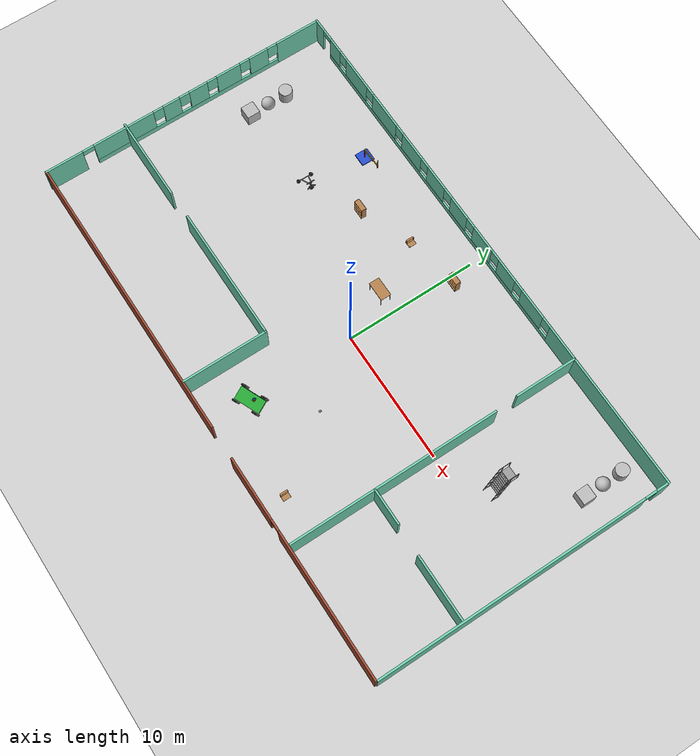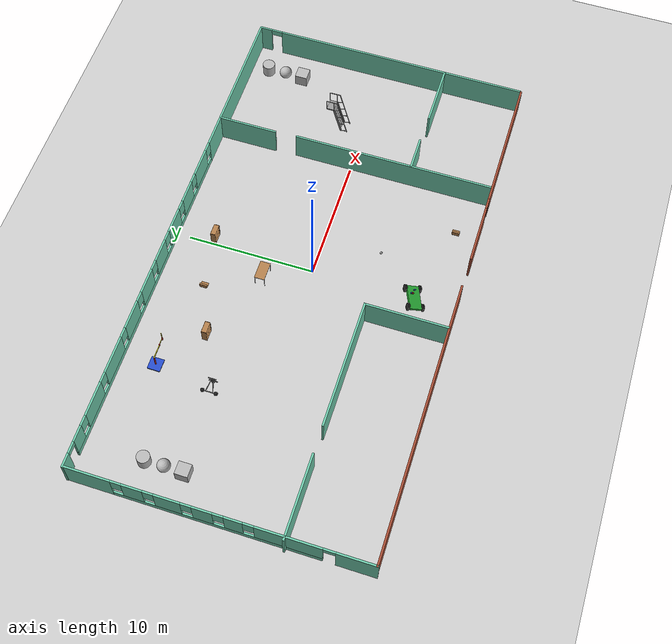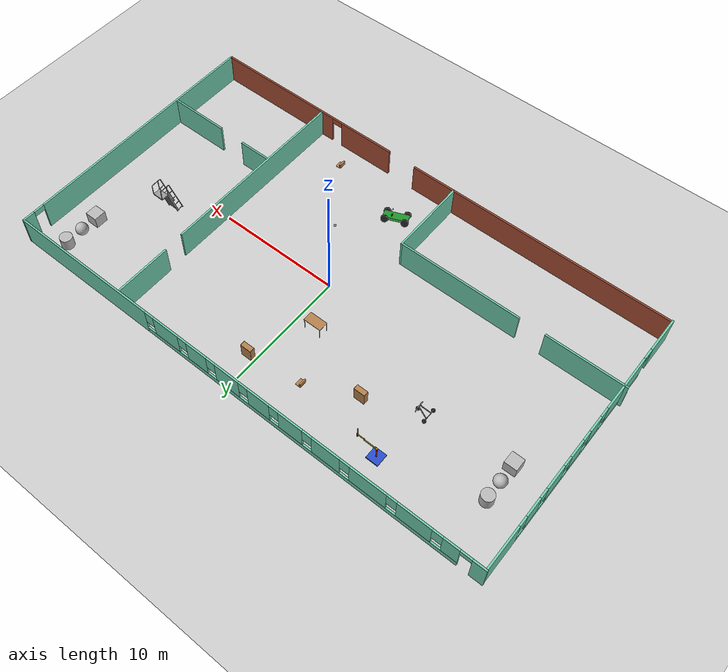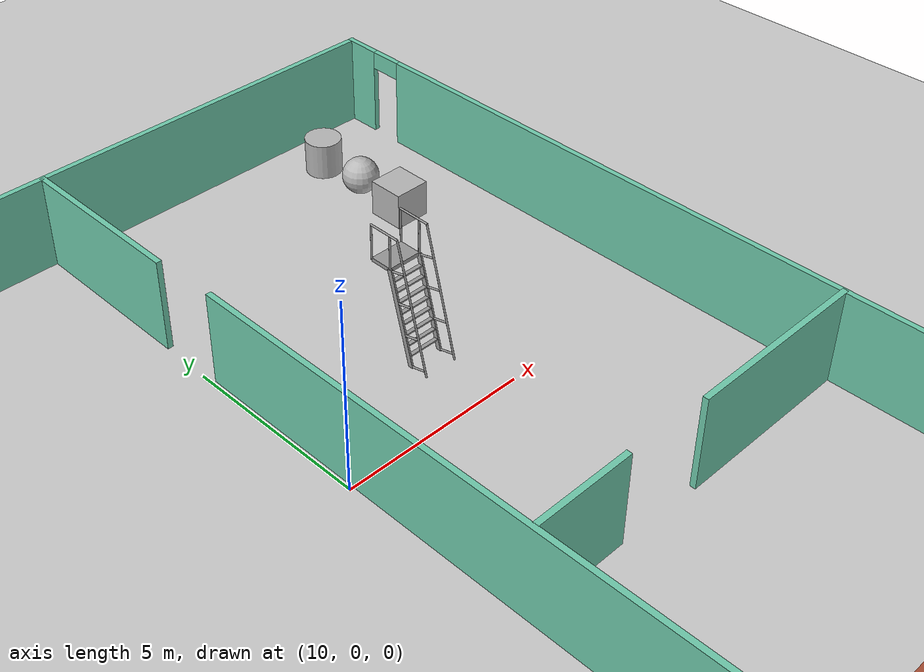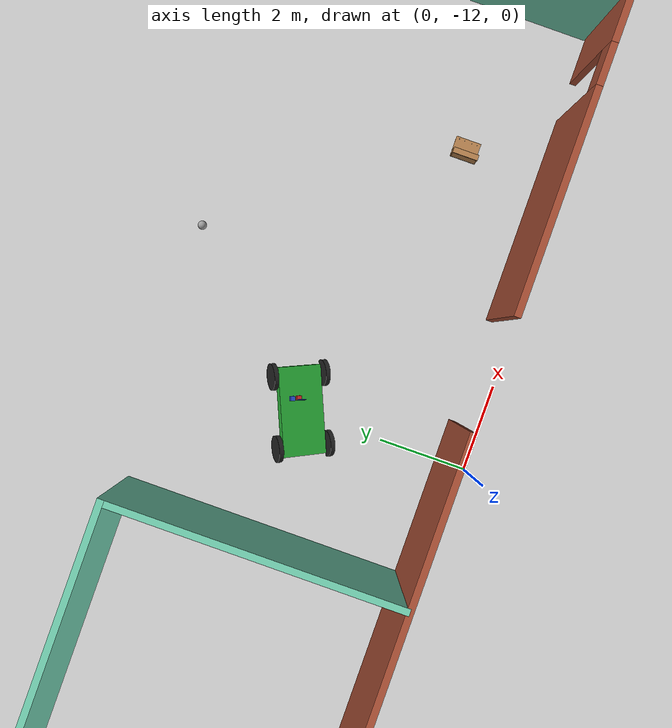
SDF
<sdf version="1.6">
 <world name="default">
  <plugin name="hello" filename="libhello.so"/>
  <light name="sun" type="directional">
   <pose>0 0 10 0 -0 0</pose>
   <diffuse>0.8 0.8 0.8 1</diffuse>
   <specular>0.2 0.2 0.2 1</specular>
   <attenuation>
    <range>1000</range>
    <constant>0.9</constant>
    <linear>0.01</linear>
    <quadratic>0.001</quadratic>
   </attenuation>
   <direction>-0.5 0.1 -0.9</direction>
  </light>
  <model name="ground_plane">
   <static>1</static>
   <link name="link">
    <collision name="collision">
     <geometry><plane><normal>0 0 1</normal><size>100 100</size></plane></geometry>
     <surface>
      <contact><collide_bitmask>65535</collide_bitmask></contact>
      <friction><ode><mu>100</mu><mu2>50</mu2></ode></friction>
     </surface>
    </collision>
    <visual name="visual">
     <cast_shadows>0</cast_shadows>
     <geometry><plane><normal>0 0 1</normal><size>100 100</size></plane></geometry>
     <material>
      <script><uri>file://media/materials/scripts/gazebo.material</uri><name>Gazebo/Grey</name></script>
     </material>
    </visual>
   </link>
  </model>
  <gravity>0 0 -9.8</gravity>
  <magnetic_field>6e-06 2.3e-05 -4.2e-05</magnetic_field>
  <atmosphere type="adiabatic"/>
  <physics name="default_physics" default="0" type="ode">
   <max_step_size>0.001</max_step_size>
   <real_time_factor>1</real_time_factor>
   <real_time_update_rate>1000</real_time_update_rate>
  </physics>
  <scene><ambient>0.4 0.4 0.4 1</ambient><background>0.7 0.7 0.7 1</background><shadows>1</shadows></scene>
  <spherical_coordinates>
   <surface_model>EARTH_WGS84</surface_model>
   <latitude_deg>0</latitude_deg>
   <longitude_deg>0</longitude_deg>
   <elevation>0</elevation>
   <heading_deg>0</heading_deg>
  </spherical_coordinates>
  <model name="office">
   <pose>-0.6589 -0.171152 0 0 -0 0</pose>
   <link name="Wall_0">
    <pose>-20.5476 -0.068828 0 0 0 -1.5708</pose>
    <visual name="Wall_0_Visual_0">
     <pose>-9.5312 0 1.25 0 -0 0</pose>
     <geometry><box><size>3.4376 0.15 2.5</size></box></geometry>
     <material>
      <script><uri>file://media/materials/scripts/gazebo.material</uri><name>Gazebo/Grey</name></script>
      <ambient>0.435294 0.796078 0.67451 1</ambient>
     </material>
     <meta><layer>0</layer></meta>
    </visual>
    <collision name="Wall_0_Collision_0">
     <geometry><box><size>3.4376 0.15 2.5</size></box></geometry>
     <pose>-9.5312 0 1.25 0 -0 0</pose>
    </collision>
    <visual name="Wall_0_Visual_1">
     <pose>9.76077 0 1.25 0 -0 0</pose>
     <geometry><box><size>2.97847 0.15 2.5</size></box></geometry>
     <material>
      <script><uri>file://media/materials/scripts/gazebo.material</uri><name>Gazebo/Grey</name></script>
      <ambient>0.435294 0.796078 0.67451 1</ambient>
     </material>
     <meta><layer>0</layer></meta>
    </visual>
    <collision name="Wall_0_Collision_1">
     <geometry><box><size>2.97847 0.15 2.5</size></box></geometry>
     <pose>9.76077 0 1.25 0 -0 0</pose>
    </collision>
    <visual name="Wall_0_Visual_2">
     <pose>-0.220435 0 0.25 0 -0 0</pose>
     <geometry><box><size>15.1839 0.15 0.5</size></box></geometry>
     <material>
      <script><uri>file://media/materials/scripts/gazebo.material</uri><name>Gazebo/Grey</name></script>
      <ambient>0.435294 0.796078 0.67451 1</ambient>
     </material>
     <meta><layer>0</layer></meta>
    </visual>
    <collision name="Wall_0_Collision_2">
     <geometry><box><size>15.1839 0.15 0.5</size></box></geometry>
     <pose>-0.220435 0 0.25 0 -0 0</pose>
    </collision>
    <visual name="Wall_0_Visual_3">
     <pose>-6.24233 0 1.5 0 -0 0</pose>
     <geometry><box><size>1.54015 0.15 2</size></box></geometry>
     <material>
      <script><uri>file://media/materials/scripts/gazebo.material</uri><name>Gazebo/Grey</name></script>
      <ambient>0.435294 0.796078 0.67451 1</ambient>
     </material>
     <meta><layer>0</layer></meta>
    </visual>
    <collision name="Wall_0_Collision_3">
     <geometry><box><size>1.54015 0.15 2</size></box></geometry>
     <pose>-6.24233 0 1.5 0 -0 0</pose>
    </collision>
    <visual name="Wall_0_Visual_4">
     <pose>-3.69569 0 1.5 0 -0 0</pose>
     <geometry><box><size>1.95312 0.15 2</size></box></geometry>
     <material>
      <script><uri>file://media/materials/scripts/gazebo.material</uri><name>Gazebo/Grey</name></script>
      <ambient>0.435294 0.796078 0.67451 1</ambient>
     </material>
     <meta><layer>0</layer></meta>
    </visual>
    <collision name="Wall_0_Collision_4">
     <geometry><box><size>1.95312 0.15 2</size></box></geometry>
     <pose>-3.69569 0 1.5 0 -0 0</pose>
    </collision>
    <visual name="Wall_0_Visual_5">
     <pose>-1.17199 0 1.5 0 -0 0</pose>
     <geometry><box><size>1.49427 0.15 2</size></box></geometry>
     <material>
      <script><uri>file://media/materials/scripts/gazebo.material</uri><name>Gazebo/Grey</name></script>
      <ambient>0.435294 0.796078 0.67451 1</ambient>
     </material>
     <meta><layer>0</layer></meta>
    </visual>
    <collision name="Wall_0_Collision_5">
     <geometry><box><size>1.49427 0.15 2</size></box></geometry>
     <pose>-1.17199 0 1.5 0 -0 0</pose>
    </collision>
    <visual name="Wall_0_Visual_6">
     <pose>1.05344 0 1.5 0 -0 0</pose>
     <geometry><box><size>1.35661 0.15 2</size></box></geometry>
     <material>
      <script><uri>file://media/materials/scripts/gazebo.material</uri><name>Gazebo/Grey</name></script>
      <ambient>0.435294 0.796078 0.67451 1</ambient>
     </material>
     <meta><layer>0</layer></meta>
    </visual>
    <collision name="Wall_0_Collision_6">
     <geometry><box><size>1.35661 0.15 2</size></box></geometry>
     <pose>1.05344 0 1.5 0 -0 0</pose>
    </collision>
    <visual name="Wall_0_Visual_7">
     <pose>4.95164 0 1.5 0 -0 0</pose>
     <geometry><box><size>4.83978 0.15 2</size></box></geometry>
     <material>
      <script><uri>file://media/materials/scripts/gazebo.material</uri><name>Gazebo/Grey</name></script>
      <ambient>0.435294 0.796078 0.67451 1</ambient>
     </material>
     <meta><layer>0</layer></meta>
    </visual>
    <collision name="Wall_0_Collision_7">
     <geometry><box><size>4.83978 0.15 2</size></box></geometry>
     <pose>4.95164 0 1.5 0 -0 0</pose>
    </collision>
    <visual name="Wall_0_Visual_8">
     <pose>-7.4124 0 1.9 0 -0 0</pose>
     <geometry><box><size>0.8 0.15 1.2</size></box></geometry>
     <material>
      <script><uri>file://media/materials/scripts/gazebo.material</uri><name>Gazebo/Grey</name></script>
      <ambient>0.435294 0.796078 0.67451 1</ambient>
     </material>
     <meta><layer>0</layer></meta>
    </visual>
    <collision name="Wall_0_Collision_8">
     <geometry><box><size>0.8 0.15 1.2</size></box></geometry>
     <pose>-7.4124 0 1.9 0 -0 0</pose>
    </collision>
    <visual name="Wall_0_Visual_9">
     <pose>-5.07225 0 1.9 0 -0 0</pose>
     <geometry><box><size>0.8 0.15 1.2</size></box></geometry>
     <material>
      <script><uri>file://media/materials/scripts/gazebo.material</uri><name>Gazebo/Grey</name></script>
      <ambient>0.435294 0.796078 0.67451 1</ambient>
     </material>
     <meta><layer>0</layer></meta>
    </visual>
    <collision name="Wall_0_Collision_9">
     <geometry><box><size>0.8 0.15 1.2</size></box></geometry>
     <pose>-5.07225 0 1.9 0 -0 0</pose>
    </collision>
    <visual name="Wall_0_Visual_10">
     <pose>-2.31913 0 1.9 0 -0 0</pose>
     <geometry><box><size>0.8 0.15 1.2</size></box></geometry>
     <material>
      <script><uri>file://media/materials/scripts/gazebo.material</uri><name>Gazebo/Grey</name></script>
      <ambient>0.435294 0.796078 0.67451 1</ambient>
     </material>
     <meta><layer>0</layer></meta>
    </visual>
    <collision name="Wall_0_Collision_10">
     <geometry><box><size>0.8 0.15 1.2</size></box></geometry>
     <pose>-2.31913 0 1.9 0 -0 0</pose>
    </collision>
    <visual name="Wall_0_Visual_11">
     <pose>-0.024862 0 1.9 0 -0 0</pose>
     <geometry><box><size>0.8 0.15 1.2</size></box></geometry>
     <material>
      <script><uri>file://media/materials/scripts/gazebo.material</uri><name>Gazebo/Grey</name></script>
      <ambient>0.435294 0.796078 0.67451 1</ambient>
     </material>
     <meta><layer>0</layer></meta>
    </visual>
    <collision name="Wall_0_Collision_11">
     <geometry><box><size>0.8 0.15 1.2</size></box></geometry>
     <pose>-0.024862 0 1.9 0 -0 0</pose>
    </collision>
    <visual name="Wall_0_Visual_12">
     <pose>2.13175 0 1.9 0 -0 0</pose>
     <geometry><box><size>0.8 0.15 1.2</size></box></geometry>
     <material>
      <script><uri>file://media/materials/scripts/gazebo.material</uri><name>Gazebo/Grey</name></script>
      <ambient>0.435294 0.796078 0.67451 1</ambient>
     </material>
     <meta><layer>0</layer></meta>
    </visual>
    <collision name="Wall_0_Collision_12">
     <geometry><box><size>0.8 0.15 1.2</size></box></geometry>
     <pose>2.13175 0 1.9 0 -0 0</pose>
    </collision>
    <visual name="Wall_0_Visual_13">
     <pose>7.82153 0 2.25 0 -0 0</pose>
     <geometry><box><size>0.9 0.15 0.5</size></box></geometry>
     <material>
      <script><uri>file://media/materials/scripts/gazebo.material</uri><name>Gazebo/Grey</name></script>
      <ambient>0.435294 0.796078 0.67451 1</ambient>
     </material>
     <meta><layer>0</layer></meta>
    </visual>
    <collision name="Wall_0_Collision_13">
     <geometry><box><size>0.9 0.15 0.5</size></box></geometry>
     <pose>7.82153 0 2.25 0 -0 0</pose>
    </collision>
   </link>
   <link name="Wall_11">
    <collision name="Wall_11_Collision">
     <geometry><box><size>5 0.15 2.5</size></box></geometry>
     <pose>0 0 1.25 0 -0 0</pose>
    </collision>
    <visual name="Wall_11_Visual">
     <pose>0 0 1.25 0 -0 0</pose>
     <geometry><box><size>5 0.15 2.5</size></box></geometry>
     <material>
      <script><uri>file://media/materials/scripts/gazebo.material</uri><name>Gazebo/Grey</name></script>
      <ambient>0.435294 0.796078 0.67451 1</ambient>
     </material>
     <meta><layer>0</layer></meta>
    </visual>
    <pose>18.3103 -4.77016 0 0 -0 0</pose>
   </link>
   <link name="Wall_13">
    <collision name="Wall_13_Collision">
     <geometry><box><size>6.5 0.15 2.5</size></box></geometry>
     <pose>0 0 1.25 0 -0 0</pose>
    </collision>
    <visual name="Wall_13_Visual">
     <pose>0 0 1.25 0 -0 0</pose>
     <geometry><box><size>6.5 0.15 2.5</size></box></geometry>
     <material>
      <script><uri>file://media/materials/scripts/gazebo.material</uri><name>Gazebo/Grey</name></script>
      <ambient>0.435294 0.796078 0.67451 1</ambient>
     </material>
     <meta><layer>0</layer></meta>
    </visual>
    <pose>-17.6021 -4.77016 0 0 -0 0</pose>
   </link>
   <link name="Wall_15">
    <collision name="Wall_15_Collision">
     <geometry><box><size>10.25 0.15 2.5</size></box></geometry>
     <pose>0 0 1.25 0 -0 0</pose>
    </collision>
    <visual name="Wall_15_Visual">
     <pose>0 0 1.25 0 -0 0</pose>
     <geometry><box><size>10.25 0.15 2.5</size></box></geometry>
     <material>
      <script><uri>file://media/materials/scripts/gazebo.material</uri><name>Gazebo/Grey</name></script>
      <ambient>0.435294 0.796078 0.67451 1</ambient>
     </material>
     <meta><layer>0</layer></meta>
    </visual>
    <pose>-7.1465 -4.77016 0 0 -0 0</pose>
   </link>
   <link name="Wall_16">
    <collision name="Wall_16_Collision">
     <geometry><box><size>6.5 0.15 2.5</size></box></geometry>
     <pose>0 0 1.25 0 -0 0</pose>
    </collision>
    <visual name="Wall_16_Visual">
     <pose>0 0 1.25 0 -0 0</pose>
     <geometry><box><size>6.5 0.15 2.5</size></box></geometry>
     <material>
      <script><uri>file://media/materials/scripts/gazebo.material</uri><name>Gazebo/Grey</name></script>
      <ambient>0.435294 0.796078 0.67451 1</ambient>
     </material>
     <meta><layer>0</layer></meta>
    </visual>
    <pose>-2.0965 -7.94516 0 0 0 -1.5708</pose>
   </link>
   <link name="Wall_18">
    <collision name="Wall_18_Collision">
     <geometry><box><size>22.25 0.15 2.5</size></box></geometry>
     <pose>0 0 1.25 0 -0 0</pose>
    </collision>
    <visual name="Wall_18_Visual">
     <pose>0 0 1.25 0 -0 0</pose>
     <geometry><box><size>22.25 0.15 2.5</size></box></geometry>
     <material>
      <script><uri>file://media/materials/scripts/gazebo.material</uri><name>Gazebo/Bricks</name></script>
      <ambient>1 1 1 1</ambient>
     </material>
     <meta><layer>0</layer></meta>
    </visual>
    <pose>-9.49763 -11.1979 0 0 -0 0</pose>
   </link>
   <link name="Wall_2">
    <pose>20.7771 0.068828 0 0 -0 1.5708</pose>
    <visual name="Wall_2_Visual_0">
     <pose>-0.973723 0 1.25 0 -0 0</pose>
     <geometry><box><size>20.5526 0.15 2.5</size></box></geometry>
     <material>
      <script><uri>file://media/materials/scripts/gazebo.material</uri><name>Gazebo/Grey</name></script>
      <ambient>0.435294 0.796078 0.67451 1</ambient>
     </material>
     <meta><layer>0</layer></meta>
    </visual>
    <collision name="Wall_2_Collision_0">
     <geometry><box><size>20.5526 0.15 2.5</size></box></geometry>
     <pose>-0.973723 0 1.25 0 -0 0</pose>
    </collision>
    <visual name="Wall_2_Visual_1">
     <pose>10.7263 0 1.25 0 -0 0</pose>
     <geometry><box><size>1.04745 0.15 2.5</size></box></geometry>
     <material>
      <script><uri>file://media/materials/scripts/gazebo.material</uri><name>Gazebo/Grey</name></script>
      <ambient>0.435294 0.796078 0.67451 1</ambient>
     </material>
     <meta><layer>0</layer></meta>
    </visual>
    <collision name="Wall_2_Collision_1">
     <geometry><box><size>1.04745 0.15 2.5</size></box></geometry>
     <pose>10.7263 0 1.25 0 -0 0</pose>
    </collision>
    <visual name="Wall_2_Visual_2">
     <pose>9.75255 0 2.25 0 -0 0</pose>
     <geometry><box><size>0.9 0.15 0.5</size></box></geometry>
     <material>
      <script><uri>file://media/materials/scripts/gazebo.material</uri><name>Gazebo/Grey</name></script>
      <ambient>0.435294 0.796078 0.67451 1</ambient>
     </material>
     <meta><layer>0</layer></meta>
    </visual>
    <collision name="Wall_2_Collision_2">
     <geometry><box><size>0.9 0.15 0.5</size></box></geometry>
     <pose>9.75255 0 2.25 0 -0 0</pose>
    </collision>
   </link>
   <link name="Wall_22">
    <pose>12.4086 -11.24 0 0 -0 0</pose>
    <visual name="Wall_22_Visual_0">
     <pose>-5.9779 0 1.25 0 -0 0</pose>
     <geometry><box><size>4.79421 0.15 2.5</size></box></geometry>
     <material>
      <script><uri>file://media/materials/scripts/gazebo.material</uri><name>Gazebo/Bricks</name></script>
      <ambient>1 1 1 1</ambient>
     </material>
     <meta><layer>0</layer></meta>
    </visual>
    <collision name="Wall_22_Collision_0">
     <geometry><box><size>4.79421 0.15 2.5</size></box></geometry>
     <pose>-5.9779 0 1.25 0 -0 0</pose>
    </collision>
    <visual name="Wall_22_Visual_1">
     <pose>2.8471 0 1.25 0 -0 0</pose>
     <geometry><box><size>11.0558 0.15 2.5</size></box></geometry>
     <material>
      <script><uri>file://media/materials/scripts/gazebo.material</uri><name>Gazebo/Bricks</name></script>
      <ambient>1 1 1 1</ambient>
     </material>
     <meta><layer>0</layer></meta>
    </visual>
    <collision name="Wall_22_Collision_1">
     <geometry><box><size>11.0558 0.15 2.5</size></box></geometry>
     <pose>2.8471 0 1.25 0 -0 0</pose>
    </collision>
    <visual name="Wall_22_Visual_2">
     <pose>-3.13079 0 2.25 0 -0 0</pose>
     <geometry><box><size>0.9 0.15 0.5</size></box></geometry>
     <material>
      <script><uri>file://media/materials/scripts/gazebo.material</uri><name>Gazebo/Bricks</name></script>
      <ambient>1 1 1 1</ambient>
     </material>
     <meta><layer>0</layer></meta>
    </visual>
    <collision name="Wall_22_Collision_2">
     <geometry><box><size>0.9 0.15 0.5</size></box></geometry>
     <pose>-3.13079 0 2.25 0 -0 0</pose>
    </collision>
   </link>
   <link name="Wall_3">
    <pose>0.102057 11.2438 0 0 -0 3.14159</pose>
    <visual name="Wall_3_Visual_0">
     <pose>-14.3599 0 1.25 0 -0 0</pose>
     <geometry><box><size>12.7802 0.15 2.5</size></box></geometry>
     <material>
      <script><uri>file://media/materials/scripts/gazebo.material</uri><name>Gazebo/Grey</name></script>
      <ambient>0.435294 0.796078 0.67451 1</ambient>
     </material>
     <meta><layer>0</layer></meta>
    </visual>
    <collision name="Wall_3_Collision_0">
     <geometry><box><size>12.7802 0.15 2.5</size></box></geometry>
     <pose>-14.3599 0 1.25 0 -0 0</pose>
    </collision>
    <visual name="Wall_3_Visual_1">
     <pose>20.2136 0 1.25 0 -0 0</pose>
     <geometry><box><size>1.07276 0.15 2.5</size></box></geometry>
     <material>
      <script><uri>file://media/materials/scripts/gazebo.material</uri><name>Gazebo/Grey</name></script>
      <ambient>0.435294 0.796078 0.67451 1</ambient>
     </material>
     <meta><layer>0</layer></meta>
    </visual>
    <collision name="Wall_3_Collision_1">
     <geometry><box><size>1.07276 0.15 2.5</size></box></geometry>
     <pose>20.2136 0 1.25 0 -0 0</pose>
    </collision>
    <visual name="Wall_3_Visual_2">
     <pose>5.40372 0 0.25 0 -0 0</pose>
     <geometry><box><size>26.747 0.15 0.5</size></box></geometry>
     <material>
      <script><uri>file://media/materials/scripts/gazebo.material</uri><name>Gazebo/Grey</name></script>
      <ambient>0.435294 0.796078 0.67451 1</ambient>
     </material>
     <meta><layer>0</layer></meta>
    </visual>
    <collision name="Wall_3_Collision_2">
     <geometry><box><size>26.747 0.15 0.5</size></box></geometry>
     <pose>5.40372 0 0.25 0 -0 0</pose>
    </collision>
    <visual name="Wall_3_Visual_3">
     <pose>-5.98675 0 1.5 0 -0 0</pose>
     <geometry><box><size>2.36609 0.15 2</size></box></geometry>
     <material>
      <script><uri>file://media/materials/scripts/gazebo.material</uri><name>Gazebo/Grey</name></script>
      <ambient>0.435294 0.796078 0.67451 1</ambient>
     </material>
     <meta><layer>0</layer></meta>
    </visual>
    <collision name="Wall_3_Collision_3">
     <geometry><box><size>2.36609 0.15 2</size></box></geometry>
     <pose>-5.98675 0 1.5 0 -0 0</pose>
    </collision>
    <visual name="Wall_3_Visual_4">
     <pose>-3.07303 0 1.5 0 -0 0</pose>
     <geometry><box><size>1.86135 0.15 2</size></box></geometry>
     <material>
      <script><uri>file://media/materials/scripts/gazebo.material</uri><name>Gazebo/Grey</name></script>
      <ambient>0.435294 0.796078 0.67451 1</ambient>
     </material>
     <meta><layer>0</layer></meta>
    </visual>
    <collision name="Wall_3_Collision_4">
     <geometry><box><size>1.86135 0.15 2</size></box></geometry>
     <pose>-3.07303 0 1.5 0 -0 0</pose>
    </collision>
    <visual name="Wall_3_Visual_5">
     <pose>-0.274028 0 1.5 0 -0 0</pose>
     <geometry><box><size>2.13666 0.15 2</size></box></geometry>
     <material>
      <script><uri>file://media/materials/scripts/gazebo.material</uri><name>Gazebo/Grey</name></script>
      <ambient>0.435294 0.796078 0.67451 1</ambient>
     </material>
     <meta><layer>0</layer></meta>
    </visual>
    <collision name="Wall_3_Collision_5">
     <geometry><box><size>2.13666 0.15 2</size></box></geometry>
     <pose>-0.274028 0 1.5 0 -0 0</pose>
    </collision>
    <visual name="Wall_3_Visual_6">
     <pose>2.54792 0 1.5 0 -0 0</pose>
     <geometry><box><size>1.90724 0.15 2</size></box></geometry>
     <material>
      <script><uri>file://media/materials/scripts/gazebo.material</uri><name>Gazebo/Grey</name></script>
      <ambient>0.435294 0.796078 0.67451 1</ambient>
     </material>
     <meta><layer>0</layer></meta>
    </visual>
    <collision name="Wall_3_Collision_6">
     <geometry><box><size>1.90724 0.15 2</size></box></geometry>
     <pose>2.54792 0 1.5 0 -0 0</pose>
    </collision>
    <visual name="Wall_3_Visual_7">
     <pose>5.32398 0 1.5 0 -0 0</pose>
     <geometry><box><size>2.04489 0.15 2</size></box></geometry>
     <material>
      <script><uri>file://media/materials/scripts/gazebo.material</uri><name>Gazebo/Grey</name></script>
      <ambient>0.435294 0.796078 0.67451 1</ambient>
     </material>
     <meta><layer>0</layer></meta>
    </visual>
    <collision name="Wall_3_Collision_7">
     <geometry><box><size>2.04489 0.15 2</size></box></geometry>
     <pose>5.32398 0 1.5 0 -0 0</pose>
    </collision>
    <visual name="Wall_3_Visual_8">
     <pose>8.30653 0 1.5 0 -0 0</pose>
     <geometry><box><size>2.3202 0.15 2</size></box></geometry>
     <material>
      <script><uri>file://media/materials/scripts/gazebo.material</uri><name>Gazebo/Grey</name></script>
      <ambient>0.435294 0.796078 0.67451 1</ambient>
     </material>
     <meta><layer>0</layer></meta>
    </visual>
    <collision name="Wall_3_Collision_8">
     <geometry><box><size>2.3202 0.15 2</size></box></geometry>
     <pose>8.30653 0 1.5 0 -0 0</pose>
    </collision>
    <visual name="Wall_3_Visual_9">
     <pose>11.7479 0 1.5 0 -0 0</pose>
     <geometry><box><size>2.9626 0.15 2</size></box></geometry>
     <material>
      <script><uri>file://media/materials/scripts/gazebo.material</uri><name>Gazebo/Grey</name></script>
      <ambient>0.435294 0.796078 0.67451 1</ambient>
     </material>
     <meta><layer>0</layer></meta>
    </visual>
    <collision name="Wall_3_Collision_9">
     <geometry><box><size>2.9626 0.15 2</size></box></geometry>
     <pose>11.7479 0 1.5 0 -0 0</pose>
    </collision>
    <visual name="Wall_3_Visual_10">
     <pose>15.3729 0 1.5 0 -0 0</pose>
     <geometry><box><size>2.68729 0.15 2</size></box></geometry>
     <material>
      <script><uri>file://media/materials/scripts/gazebo.material</uri><name>Gazebo/Grey</name></script>
      <ambient>0.435294 0.796078 0.67451 1</ambient>
     </material>
     <meta><layer>0</layer></meta>
    </visual>
    <collision name="Wall_3_Collision_10">
     <geometry><box><size>2.68729 0.15 2</size></box></geometry>
     <pose>15.3729 0 1.5 0 -0 0</pose>
    </collision>
    <visual name="Wall_3_Visual_11">
     <pose>18.1469 0 1.5 0 -0 0</pose>
     <geometry><box><size>1.26073 0.15 2</size></box></geometry>
     <material>
      <script><uri>file://media/materials/scripts/gazebo.material</uri><name>Gazebo/Grey</name></script>
      <ambient>0.435294 0.796078 0.67451 1</ambient>
     </material>
     <meta><layer>0</layer></meta>
    </visual>
    <collision name="Wall_3_Collision_11">
     <geometry><box><size>1.26073 0.15 2</size></box></geometry>
     <pose>18.1469 0 1.5 0 -0 0</pose>
    </collision>
    <visual name="Wall_3_Visual_12">
     <pose>-7.5698 0 1.9 0 -0 0</pose>
     <geometry><box><size>0.8 0.15 1.2</size></box></geometry>
     <material>
      <script><uri>file://media/materials/scripts/gazebo.material</uri><name>Gazebo/Grey</name></script>
      <ambient>0.435294 0.796078 0.67451 1</ambient>
     </material>
     <meta><layer>0</layer></meta>
    </visual>
    <collision name="Wall_3_Collision_12">
     <geometry><box><size>0.8 0.15 1.2</size></box></geometry>
     <pose>-7.5698 0 1.9 0 -0 0</pose>
    </collision>
    <visual name="Wall_3_Visual_13">
     <pose>-4.40371 0 1.9 0 -0 0</pose>
     <geometry><box><size>0.8 0.15 1.2</size></box></geometry>
     <material>
      <script><uri>file://media/materials/scripts/gazebo.material</uri><name>Gazebo/Grey</name></script>
      <ambient>0.435294 0.796078 0.67451 1</ambient>
     </material>
     <meta><layer>0</layer></meta>
    </visual>
    <collision name="Wall_3_Collision_13">
     <geometry><box><size>0.8 0.15 1.2</size></box></geometry>
     <pose>-4.40371 0 1.9 0 -0 0</pose>
    </collision>
    <visual name="Wall_3_Visual_14">
     <pose>-1.74236 0 1.9 0 -0 0</pose>
     <geometry><box><size>0.8 0.15 1.2</size></box></geometry>
     <material>
      <script><uri>file://media/materials/scripts/gazebo.material</uri><name>Gazebo/Grey</name></script>
      <ambient>0.435294 0.796078 0.67451 1</ambient>
     </material>
     <meta><layer>0</layer></meta>
    </visual>
    <collision name="Wall_3_Collision_14">
     <geometry><box><size>0.8 0.15 1.2</size></box></geometry>
     <pose>-1.74236 0 1.9 0 -0 0</pose>
    </collision>
    <visual name="Wall_3_Visual_15">
     <pose>1.1943 0 1.9 0 -0 0</pose>
     <geometry><box><size>0.8 0.15 1.2</size></box></geometry>
     <material>
      <script><uri>file://media/materials/scripts/gazebo.material</uri><name>Gazebo/Grey</name></script>
      <ambient>0.435294 0.796078 0.67451 1</ambient>
     </material>
     <meta><layer>0</layer></meta>
    </visual>
    <collision name="Wall_3_Collision_15">
     <geometry><box><size>0.8 0.15 1.2</size></box></geometry>
     <pose>1.1943 0 1.9 0 -0 0</pose>
    </collision>
    <visual name="Wall_3_Visual_16">
     <pose>3.90154 0 1.9 0 -0 0</pose>
     <geometry><box><size>0.8 0.15 1.2</size></box></geometry>
     <material>
      <script><uri>file://media/materials/scripts/gazebo.material</uri><name>Gazebo/Grey</name></script>
      <ambient>0.435294 0.796078 0.67451 1</ambient>
     </material>
     <meta><layer>0</layer></meta>
    </visual>
    <collision name="Wall_3_Collision_16">
     <geometry><box><size>0.8 0.15 1.2</size></box></geometry>
     <pose>3.90154 0 1.9 0 -0 0</pose>
    </collision>
    <visual name="Wall_3_Visual_17">
     <pose>6.74643 0 1.9 0 -0 0</pose>
     <geometry><box><size>0.8 0.15 1.2</size></box></geometry>
     <material>
      <script><uri>file://media/materials/scripts/gazebo.material</uri><name>Gazebo/Grey</name></script>
      <ambient>0.435294 0.796078 0.67451 1</ambient>
     </material>
     <meta><layer>0</layer></meta>
    </visual>
    <collision name="Wall_3_Collision_17">
     <geometry><box><size>0.8 0.15 1.2</size></box></geometry>
     <pose>6.74643 0 1.9 0 -0 0</pose>
    </collision>
    <visual name="Wall_3_Visual_18">
     <pose>9.86663 0 1.9 0 -0 0</pose>
     <geometry><box><size>0.8 0.15 1.2</size></box></geometry>
     <material>
      <script><uri>file://media/materials/scripts/gazebo.material</uri><name>Gazebo/Grey</name></script>
      <ambient>0.435294 0.796078 0.67451 1</ambient>
     </material>
     <meta><layer>0</layer></meta>
    </visual>
    <collision name="Wall_3_Collision_18">
     <geometry><box><size>0.8 0.15 1.2</size></box></geometry>
     <pose>9.86663 0 1.9 0 -0 0</pose>
    </collision>
    <visual name="Wall_3_Visual_19">
     <pose>13.6292 0 1.9 0 -0 0</pose>
     <geometry><box><size>0.8 0.15 1.2</size></box></geometry>
     <material>
      <script><uri>file://media/materials/scripts/gazebo.material</uri><name>Gazebo/Grey</name></script>
      <ambient>0.435294 0.796078 0.67451 1</ambient>
     </material>
     <meta><layer>0</layer></meta>
    </visual>
    <collision name="Wall_3_Collision_19">
     <geometry><box><size>0.8 0.15 1.2</size></box></geometry>
     <pose>13.6292 0 1.9 0 -0 0</pose>
    </collision>
    <visual name="Wall_3_Visual_20">
     <pose>17.1165 0 1.9 0 -0 0</pose>
     <geometry><box><size>0.8 0.15 1.2</size></box></geometry>
     <material>
      <script><uri>file://media/materials/scripts/gazebo.material</uri><name>Gazebo/Grey</name></script>
      <ambient>0.435294 0.796078 0.67451 1</ambient>
     </material>
     <meta><layer>0</layer></meta>
    </visual>
    <collision name="Wall_3_Collision_20">
     <geometry><box><size>0.8 0.15 1.2</size></box></geometry>
     <pose>17.1165 0 1.9 0 -0 0</pose>
    </collision>
    <visual name="Wall_3_Visual_21">
     <pose>19.2272 0 2.25 0 -0 0</pose>
     <geometry><box><size>0.9 0.15 0.5</size></box></geometry>
     <material>
      <script><uri>file://media/materials/scripts/gazebo.material</uri><name>Gazebo/Grey</name></script>
      <ambient>0.435294 0.796078 0.67451 1</ambient>
     </material>
     <meta><layer>0</layer></meta>
    </visual>
    <collision name="Wall_3_Collision_21">
     <geometry><box><size>0.9 0.15 0.5</size></box></geometry>
     <pose>19.2272 0 2.25 0 -0 0</pose>
    </collision>
   </link>
   <link name="Wall_5">
    <collision name="Wall_5_Collision">
     <geometry><box><size>4.75 0.15 2.5</size></box></geometry>
     <pose>0 0 1.25 0 -0 0</pose>
    </collision>
    <visual name="Wall_5_Visual">
     <pose>0 0 1.25 0 -0 0</pose>
     <geometry><box><size>4.75 0.15 2.5</size></box></geometry>
     <material>
      <script><uri>file://media/materials/scripts/gazebo.material</uri><name>Gazebo/Grey</name></script>
      <ambient>0.435294 0.796078 0.67451 1</ambient>
     </material>
     <meta><layer>0</layer></meta>
    </visual>
    <pose>10.7462 8.89794 0 0 0 -1.5708</pose>
   </link>
   <link name="Wall_7">
    <collision name="Wall_7_Collision">
     <geometry><box><size>16 0.15 2.5</size></box></geometry>
     <pose>0 0 1.25 0 -0 0</pose>
    </collision>
    <visual name="Wall_7_Visual">
     <pose>0 0 1.25 0 -0 0</pose>
     <geometry><box><size>16 0.15 2.5</size></box></geometry>
     <material>
      <script><uri>file://media/materials/scripts/gazebo.material</uri><name>Gazebo/Grey</name></script>
      <ambient>0.435294 0.796078 0.67451 1</ambient>
     </material>
     <meta><layer>0</layer></meta>
    </visual>
    <pose>10.8379 -3.15101 0 0 0 -1.5708</pose>
   </link>
   <link name="Wall_9">
    <collision name="Wall_9_Collision">
     <geometry><box><size>2.75 0.15 2.5</size></box></geometry>
     <pose>0 0 1.25 0 -0 0</pose>
    </collision>
    <visual name="Wall_9_Visual">
     <pose>0 0 1.25 0 -0 0</pose>
     <geometry><box><size>2.75 0.15 2.5</size></box></geometry>
     <material>
      <script><uri>file://media/materials/scripts/gazebo.material</uri><name>Gazebo/Grey</name></script>
      <ambient>0.435294 0.796078 0.67451 1</ambient>
     </material>
     <meta><layer>0</layer></meta>
    </visual>
    <pose>12.1838 -4.67839 0 0 -0 0</pose>
   </link>
   <static>1</static>
  </model>
  <model name="bookshelf">
   <static>1</static>
   <link name="link">
    <inertial><mass>1</mass></inertial>
    <collision name="back">
     <pose>0 0.005 0.6 0 -0 0</pose>
     <geometry><box><size>0.9 0.01 1.2</size></box></geometry>
    </collision>
    <visual name="visual1">
     <pose>0 0.005 0.6 0 -0 0</pose>
     <geometry><box><size>0.9 0.01 1.2</size></box></geometry>
     <material>
      <script><uri>file://media/materials/scripts/gazebo.material</uri><name>Gazebo/Wood</name></script>
     </material>
    </visual>
    <collision name="left_side">
     <pose>0.45 -0.195 0.6 0 -0 0</pose>
     <geometry><box><size>0.02 0.4 1.2</size></box></geometry>
    </collision>
    <visual name="visual2">
     <pose>0.45 -0.195 0.6 0 -0 0</pose>
     <geometry><box><size>0.02 0.4 1.2</size></box></geometry>
     <material>
      <script><uri>file://media/materials/scripts/gazebo.material</uri><name>Gazebo/Wood</name></script>
     </material>
    </visual>
    <collision name="right_side">
     <pose>-0.45 -0.195 0.6 0 -0 0</pose>
     <geometry><box><size>0.02 0.4 1.2</size></box></geometry>
    </collision>
    <visual name="visual3">
     <pose>-0.45 -0.195 0.6 0 -0 0</pose>
     <geometry><box><size>0.02 0.4 1.2</size></box></geometry>
     <material>
      <script><uri>file://media/materials/scripts/gazebo.material</uri><name>Gazebo/Wood</name></script>
     </material>
    </visual>
    <collision name="bottom">
     <pose>0 -0.195 0.03 0 -0 0</pose>
     <geometry><box><size>0.88 0.4 0.06</size></box></geometry>
    </collision>
    <visual name="visual4">
     <pose>0 -0.195 0.03 0 -0 0</pose>
     <geometry><box><size>0.88 0.4 0.06</size></box></geometry>
     <material>
      <script><uri>file://media/materials/scripts/gazebo.material</uri><name>Gazebo/Wood</name></script>
     </material>
    </visual>
    <collision name="top">
     <pose>0 -0.195 1.19 0 -0 0</pose>
     <geometry><box><size>0.88 0.4 0.02</size></box></geometry>
    </collision>
    <visual name="visual5">
     <pose>0 -0.195 1.19 0 -0 0</pose>
     <geometry><box><size>0.88 0.4 0.02</size></box></geometry>
     <material>
      <script><uri>file://media/materials/scripts/gazebo.material</uri><name>Gazebo/Wood</name></script>
     </material>
    </visual>
    <collision name="low_shelf">
     <pose>0 -0.195 0.43 0 -0 0</pose>
     <geometry><box><size>0.88 0.4 0.02</size></box></geometry>
    </collision>
    <visual name="visual6">
     <pose>0 -0.195 0.43 0 -0 0</pose>
     <geometry><box><size>0.88 0.4 0.02</size></box></geometry>
     <material>
      <script><uri>file://media/materials/scripts/gazebo.material</uri><name>Gazebo/Wood</name></script>
     </material>
    </visual>
    <collision name="high_shelf">
     <pose>0 -0.195 0.8 0 -0 0</pose>
     <geometry><box><size>0.88 0.4 0.02</size></box></geometry>
    </collision>
    <visual name="visual7">
     <pose>0 -0.195 0.8 0 -0 0</pose>
     <geometry><box><size>0.88 0.4 0.02</size></box></geometry>
     <material>
      <script><uri>file://media/materials/scripts/gazebo.material</uri><name>Gazebo/Wood</name></script>
     </material>
    </visual>
   </link>
   <pose>-7.57156 6.02556 0 0 -0 0</pose>
  </model>
  <model name="bookshelf_1">
   <static>1</static>
   <link name="link">
    <inertial><mass>1</mass></inertial>
    <collision name="back">
     <pose>0 0.005 0.6 0 -0 0</pose>
     <geometry><box><size>0.9 0.01 1.2</size></box></geometry>
    </collision>
    <visual name="visual1">
     <pose>0 0.005 0.6 0 -0 0</pose>
     <geometry><box><size>0.9 0.01 1.2</size></box></geometry>
     <material>
      <script><uri>file://media/materials/scripts/gazebo.material</uri><name>Gazebo/Wood</name></script>
     </material>
    </visual>
    <collision name="left_side">
     <pose>0.45 -0.195 0.6 0 -0 0</pose>
     <geometry><box><size>0.02 0.4 1.2</size></box></geometry>
    </collision>
    <visual name="visual2">
     <pose>0.45 -0.195 0.6 0 -0 0</pose>
     <geometry><box><size>0.02 0.4 1.2</size></box></geometry>
     <material>
      <script><uri>file://media/materials/scripts/gazebo.material</uri><name>Gazebo/Wood</name></script>
     </material>
    </visual>
    <collision name="right_side">
     <pose>-0.45 -0.195 0.6 0 -0 0</pose>
     <geometry><box><size>0.02 0.4 1.2</size></box></geometry>
    </collision>
    <visual name="visual3">
     <pose>-0.45 -0.195 0.6 0 -0 0</pose>
     <geometry><box><size>0.02 0.4 1.2</size></box></geometry>
     <material>
      <script><uri>file://media/materials/scripts/gazebo.material</uri><name>Gazebo/Wood</name></script>
     </material>
    </visual>
    <collision name="bottom">
     <pose>0 -0.195 0.03 0 -0 0</pose>
     <geometry><box><size>0.88 0.4 0.06</size></box></geometry>
    </collision>
    <visual name="visual4">
     <pose>0 -0.195 0.03 0 -0 0</pose>
     <geometry><box><size>0.88 0.4 0.06</size></box></geometry>
     <material>
      <script><uri>file://media/materials/scripts/gazebo.material</uri><name>Gazebo/Wood</name></script>
     </material>
    </visual>
    <collision name="top">
     <pose>0 -0.195 1.19 0 -0 0</pose>
     <geometry><box><size>0.88 0.4 0.02</size></box></geometry>
    </collision>
    <visual name="visual5">
     <pose>0 -0.195 1.19 0 -0 0</pose>
     <geometry><box><size>0.88 0.4 0.02</size></box></geometry>
     <material>
      <script><uri>file://media/materials/scripts/gazebo.material</uri><name>Gazebo/Wood</name></script>
     </material>
    </visual>
    <collision name="low_shelf">
     <pose>0 -0.195 0.43 0 -0 0</pose>
     <geometry><box><size>0.88 0.4 0.02</size></box></geometry>
    </collision>
    <visual name="visual6">
     <pose>0 -0.195 0.43 0 -0 0</pose>
     <geometry><box><size>0.88 0.4 0.02</size></box></geometry>
     <material>
      <script><uri>file://media/materials/scripts/gazebo.material</uri><name>Gazebo/Wood</name></script>
     </material>
    </visual>
    <collision name="high_shelf">
     <pose>0 -0.195 0.8 0 -0 0</pose>
     <geometry><box><size>0.88 0.4 0.02</size></box></geometry>
    </collision>
    <visual name="visual7">
     <pose>0 -0.195 0.8 0 -0 0</pose>
     <geometry><box><size>0.88 0.4 0.02</size></box></geometry>
     <material>
      <script><uri>file://media/materials/scripts/gazebo.material</uri><name>Gazebo/Wood</name></script>
     </material>
    </visual>
   </link>
   <pose>0.626571 8.34129 0 0 -0 0</pose>
  </model>
  <model name="table_1">
   <static>1</static>
   <link name="link">
    <collision name="surface">
     <pose>0 0 1 0 -0 0</pose>
     <geometry><box><size>1.5 0.8 0.03</size></box></geometry>
     <surface><friction><ode><mu>0.6</mu><mu2>0.6</mu2></ode></friction></surface>
    </collision>
    <visual name="visual1">
     <pose>0 0 1 0 -0 0</pose>
     <geometry><box><size>1.5 0.8 0.03</size></box></geometry>
     <material>
      <script><uri>file://media/materials/scripts/gazebo.material</uri><name>Gazebo/Wood</name></script>
     </material>
    </visual>
    <collision name="front_left_leg">
     <pose>0.68 0.38 0.5 0 -0 0</pose>
     <geometry><cylinder><radius>0.02</radius><length>1</length></cylinder></geometry>
    </collision>
    <visual name="front_left_leg">
     <pose>0.68 0.38 0.5 0 -0 0</pose>
     <geometry><cylinder><radius>0.02</radius><length>1</length></cylinder></geometry>
     <material>
      <script><uri>file://media/materials/scripts/gazebo.material</uri><name>Gazebo/Grey</name></script>
     </material>
    </visual>
    <collision name="front_right_leg">
     <pose>0.68 -0.38 0.5 0 -0 0</pose>
     <geometry><cylinder><radius>0.02</radius><length>1</length></cylinder></geometry>
    </collision>
    <visual name="front_right_leg">
     <pose>0.68 -0.38 0.5 0 -0 0</pose>
     <geometry><cylinder><radius>0.02</radius><length>1</length></cylinder></geometry>
     <material>
      <script><uri>file://media/materials/scripts/gazebo.material</uri><name>Gazebo/Grey</name></script>
     </material>
    </visual>
    <collision name="back_right_leg">
     <pose>-0.68 -0.38 0.5 0 -0 0</pose>
     <geometry><cylinder><radius>0.02</radius><length>1</length></cylinder></geometry>
    </collision>
    <visual name="back_right_leg">
     <pose>-0.68 -0.38 0.5 0 -0 0</pose>
     <geometry><cylinder><radius>0.02</radius><length>1</length></cylinder></geometry>
     <material>
      <script><uri>file://media/materials/scripts/gazebo.material</uri><name>Gazebo/Grey</name></script>
     </material>
    </visual>
    <collision name="back_left_leg">
     <pose>-0.68 0.38 0.5 0 -0 0</pose>
     <geometry><cylinder><radius>0.02</radius><length>1</length></cylinder></geometry>
    </collision>
    <visual name="back_left_leg">
     <pose>-0.68 0.38 0.5 0 -0 0</pose>
     <geometry><cylinder><radius>0.02</radius><length>1</length></cylinder></geometry>
     <material>
      <script><uri>file://media/materials/scripts/gazebo.material</uri><name>Gazebo/Grey</name></script>
     </material>
    </visual>
   </link>
   <pose>-1.59069 3.48064 0 0 -0 0</pose>
  </model>
  <model name="my_ball">
   <link name="link_0">
    <inertial>
     <mass>1</mass>
     <inertia><ixx>0.1</ixx><ixy>0</ixy><ixz>0</ixz><iyy>0.1</iyy><iyz>0</iyz><izz>0.1</izz></inertia>
    </inertial>
    <visual name="visual">
     <geometry><sphere><radius>0.1</radius></sphere></geometry>
     <material>
      <lighting>1</lighting>
      <script><uri>file://media/materials/scripts/gazebo.material</uri><name>Gazebo/Grey</name></script>
      <shader type="pixel"><normal_map>__default__</normal_map></shader>
      <ambient>1 1 1 1</ambient>
      <diffuse>1 1 1 1</diffuse>
      <specular>1 1 1 1</specular>
      <emissive>1 1 1 1</emissive>
     </material>
    </visual>
    <collision name="collision">
     <geometry><sphere><radius>0.1</radius></sphere></geometry>
     <surface>
      <friction>
       <ode><mu>1</mu><mu2>1</mu2><fdir1>0 0 0</fdir1><slip1>0</slip1><slip2>0</slip2></ode>
       <torsional>
        <coefficient>1</coefficient>
        <patch_radius>0</patch_radius>
        <surface_radius>0</surface_radius>
        <use_patch_radius>1</use_patch_radius>
        <ode><slip>0</slip></ode>
       </torsional>
      </friction>
      <bounce><restitution_coefficient>0</restitution_coefficient><threshold>1e+06</threshold></bounce>
      <contact>
       <collide_without_contact>0</collide_without_contact>
       <collide_without_contact_bitmask>1</collide_without_contact_bitmask>
       <collide_bitmask>1</collide_bitmask>
       <ode>
        <soft_cfm>0</soft_cfm>
        <soft_erp>0.2</soft_erp>
        <kp>1e+13</kp>
        <kd>1</kd>
        <max_vel>0.01</max_vel>
        <min_depth>0</min_depth>
       </ode>
       <bullet>
        <split_impulse>1</split_impulse>
        <split_impulse_penetration_threshold>-0.01</split_impulse_penetration_threshold>
        <soft_cfm>0</soft_cfm>
        <soft_erp>0.2</soft_erp>
        <kp>1e+13</kp>
        <kd>1</kd>
       </bullet>
      </contact>
     </surface>
    </collision>
   </link>
   <static>0</static>
   <pose>3.24396 -4.56383 0.1 0 -0 0</pose>
  </model>
  <model name="simple_arm">
   <link name="arm_base">
    <inertial>
     <pose>0 0 0.00099 0 -0 0</pose>
     <inertia><ixx>1.11</ixx><ixy>0</ixy><ixz>0</ixz><iyy>100.11</iyy><iyz>0</iyz><izz>1.01</izz></inertia>
     <mass>101</mass>
    </inertial>
    <collision name="arm_base_geom">
     <pose>0 0 0.05 0 -0 0</pose>
     <geometry><box><size>1 1 0.1</size></box></geometry>
    </collision>
    <visual name="arm_base_geom_visual">
     <pose>0 0 0.05 0 -0 0</pose>
     <geometry><box><size>1 1 0.1</size></box></geometry>
     <material>
      <script><uri>file://media/materials/scripts/gazebo.material</uri><name>Gazebo/Blue</name></script>
     </material>
    </visual>
    <collision name="arm_base_geom_arm_trunk">
     <pose>0 0 0.6 0 -0 0</pose>
     <geometry><cylinder><radius>0.05</radius><length>1</length></cylinder></geometry>
    </collision>
    <visual name="arm_base_geom_arm_trunk_visual">
     <pose>0 0 0.6 0 -0 0</pose>
     <geometry><cylinder><radius>0.05</radius><length>1</length></cylinder></geometry>
     <material>
      <script><uri>file://media/materials/scripts/gazebo.material</uri><name>Gazebo/Red</name></script>
     </material>
    </visual>
   </link>
   <link name="arm_shoulder_pan">
    <pose>0 0 1.1 0 -0 0</pose>
    <inertial>
     <pose>0.045455 0 0 0 -0 0</pose>
     <inertia><ixx>0.011</ixx><ixy>0</ixy><ixz>0</ixz><iyy>0.0225</iyy><iyz>0</iyz><izz>0.0135</izz></inertia>
     <mass>1.1</mass>
    </inertial>
    <collision name="arm_shoulder_pan_geom">
     <pose>0 0 0.05 0 -0 0</pose>
     <geometry><cylinder><radius>0.05</radius><length>0.1</length></cylinder></geometry>
    </collision>
    <visual name="arm_shoulder_pan_geom_visual">
     <pose>0 0 0.05 0 -0 0</pose>
     <geometry><cylinder><radius>0.05</radius><length>0.1</length></cylinder></geometry>
     <material>
      <script><uri>file://media/materials/scripts/gazebo.material</uri><name>Gazebo/Yellow</name></script>
     </material>
    </visual>
    <collision name="arm_shoulder_pan_geom_arm_shoulder">
     <pose>0.55 0 0.05 0 -0 0</pose>
     <geometry><box><size>1 0.05 0.1</size></box></geometry>
    </collision>
    <visual name="arm_shoulder_pan_geom_arm_shoulder_visual">
     <pose>0.55 0 0.05 0 -0 0</pose>
     <geometry><box><size>1 0.05 0.1</size></box></geometry>
     <material>
      <script><uri>file://media/materials/scripts/gazebo.material</uri><name>Gazebo/Yellow</name></script>
     </material>
    </visual>
   </link>
   <link name="arm_elbow_pan">
    <pose>1.05 0 1.1 0 -0 0</pose>
    <inertial>
     <pose>0.0875 0 0.083333 0 -0 0</pose>
     <inertia>
      <ixx>0.031</ixx>
      <ixy>0</ixy>
      <ixz>0.005</ixz>
      <iyy>0.07275</iyy>
      <iyz>0</iyz>
      <izz>0.04475</izz>
     </inertia>
     <mass>1.2</mass>
    </inertial>
    <collision name="arm_elbow_pan_geom">
     <pose>0 0 0.1 0 -0 0</pose>
     <geometry><cylinder><radius>0.05</radius><length>0.2</length></cylinder></geometry>
    </collision>
    <visual name="arm_elbow_pan_geom_visual">
     <pose>0 0 0.1 0 -0 0</pose>
     <geometry><cylinder><radius>0.05</radius><length>0.2</length></cylinder></geometry>
     <material>
      <script><uri>file://media/materials/scripts/gazebo.material</uri><name>Gazebo/Red</name></script>
     </material>
    </visual>
    <collision name="arm_elbow_pan_geom_arm_elbow">
     <pose>0.3 0 0.15 0 -0 0</pose>
     <geometry><box><size>0.5 0.03 0.1</size></box></geometry>
    </collision>
    <visual name="arm_elbow_pan_geom_arm_elbow_visual">
     <pose>0.3 0 0.15 0 -0 0</pose>
     <geometry><box><size>0.5 0.03 0.1</size></box></geometry>
     <material>
      <script><uri>file://media/materials/scripts/gazebo.material</uri><name>Gazebo/Yellow</name></script>
     </material>
    </visual>
    <collision name="arm_elbow_pan_geom_arm_wrist">
     <pose>0.55 0 0.15 0 -0 0</pose>
     <geometry><cylinder><radius>0.05</radius><length>0.3</length></cylinder></geometry>
    </collision>
    <visual name="arm_elbow_pan_geom_arm_wrist_visual">
     <pose>0.55 0 0.15 0 -0 0</pose>
     <geometry><cylinder><radius>0.05</radius><length>0.3</length></cylinder></geometry>
     <material>
      <script><uri>file://media/materials/scripts/gazebo.material</uri><name>Gazebo/Red</name></script>
     </material>
    </visual>
   </link>
   <link name="arm_wrist_lift">
    <pose>1.6 0 1.05 0 -0 0</pose>
    <inertial>
     <inertia><ixx>0.01</ixx><ixy>0</ixy><ixz>0</ixz><iyy>0.01</iyy><iyz>0</iyz><izz>0.001</izz></inertia>
     <mass>0.1</mass>
    </inertial>
    <collision name="arm_wrist_lift_geom">
     <pose>0 0 0.5 0 -0 0</pose>
     <geometry><cylinder><radius>0.03</radius><length>1</length></cylinder></geometry>
    </collision>
    <visual name="arm_wrist_lift_geom_visual">
     <pose>0 0 0.5 0 -0 0</pose>
     <geometry><cylinder><radius>0.03</radius><length>1</length></cylinder></geometry>
     <material>
      <script><uri>file://media/materials/scripts/gazebo.material</uri><name>Gazebo/Yellow</name></script>
     </material>
    </visual>
   </link>
   <link name="arm_wrist_roll">
    <pose>1.6 0 1 0 -0 0</pose>
    <inertial>
     <inertia><ixx>0.01</ixx><ixy>0</ixy><ixz>0</ixz><iyy>0.01</iyy><iyz>0</iyz><izz>0.001</izz></inertia>
     <mass>0.1</mass>
    </inertial>
    <collision name="arm_wrist_roll_geom">
     <pose>0 0 0.025 0 -0 0</pose>
     <geometry><cylinder><radius>0.05</radius><length>0.05</length></cylinder></geometry>
    </collision>
    <visual name="arm_wrist_roll_geom_visual">
     <pose>0 0 0.025 0 -0 0</pose>
     <geometry><cylinder><radius>0.05</radius><length>0.05</length></cylinder></geometry>
     <material>
      <script><uri>file://media/materials/scripts/gazebo.material</uri><name>Gazebo/Red</name></script>
     </material>
    </visual>
   </link>
   <joint name="arm_shoulder_pan_joint" type="revolute">
    <parent>arm_base</parent>
    <child>arm_shoulder_pan</child>
    <axis>
     <dynamics>
      <damping>1</damping>
      <friction>0</friction>
      <spring_reference>0</spring_reference>
      <spring_stiffness>0</spring_stiffness>
     </dynamics>
     <xyz>0 0 1</xyz>
     <use_parent_model_frame>1</use_parent_model_frame>
     <limit><lower>-1e+16</lower><upper>1e+16</upper></limit>
    </axis>
   </joint>
   <joint name="arm_elbow_pan_joint" type="revolute">
    <parent>arm_shoulder_pan</parent>
    <child>arm_elbow_pan</child>
    <axis>
     <dynamics>
      <damping>1</damping>
      <friction>0</friction>
      <spring_reference>0</spring_reference>
      <spring_stiffness>0</spring_stiffness>
     </dynamics>
     <xyz>0 0 1</xyz>
     <use_parent_model_frame>1</use_parent_model_frame>
     <limit><lower>-1e+16</lower><upper>1e+16</upper></limit>
    </axis>
   </joint>
   <joint name="arm_wrist_lift_joint" type="prismatic">
    <parent>arm_elbow_pan</parent>
    <child>arm_wrist_lift</child>
    <axis>
     <dynamics>
      <damping>1</damping>
      <friction>0</friction>
      <spring_reference>0</spring_reference>
      <spring_stiffness>0</spring_stiffness>
     </dynamics>
     <limit><lower>-0.8</lower><upper>0.1</upper></limit>
     <xyz>0 0 1</xyz>
     <use_parent_model_frame>1</use_parent_model_frame>
    </axis>
   </joint>
   <joint name="arm_wrist_roll_joint" type="revolute">
    <parent>arm_wrist_lift</parent>
    <child>arm_wrist_roll</child>
    <axis>
     <dynamics>
      <damping>1</damping>
      <friction>0</friction>
      <spring_reference>0</spring_reference>
      <spring_stiffness>0</spring_stiffness>
     </dynamics>
     <limit><lower>-2.99999</lower><upper>2.99999</upper></limit>
     <xyz>0 0 1</xyz>
     <use_parent_model_frame>1</use_parent_model_frame>
    </axis>
   </joint>
   <pose>-11.0493 8.53607 0 0 0 -0.002496</pose>
  </model>
  <model name="trisphere_cycle">
   <link name="frame">
    <pose>-0.408559 0 0.385023 0 -0.522021 0</pose>
    <inertial>
     <mass>10</mass>
     <inertia><ixx>0.228</ixx><iyy>0.743521</iyy><izz>0.965521</izz><ixy>0</ixy><ixz>0</ixz><iyz>0</iyz></inertia>
    </inertial>
    <collision name="axle_collision">
     <pose>-0.471335 0 0 1.5708 -0 0</pose>
     <geometry><cylinder><length>1.03923</length><radius>0.03</radius></cylinder></geometry>
    </collision>
    <visual name="axle_visual">
     <pose>-0.471335 0 0 1.5708 -0 0</pose>
     <geometry><cylinder><length>1.03923</length><radius>0.03</radius></cylinder></geometry>
     <material>
      <script><uri>file://media/materials/scripts/gazebo.material</uri><name>Gazebo/Grey</name></script>
     </material>
    </visual>
    <collision name="frame_left_collision">
     <pose>0 0.171552 0 2.986 1.57079 2.76675</pose>
     <geometry><cylinder><length>1.00317</length><radius>0.03</radius></cylinder></geometry>
    </collision>
    <visual name="frame_left_visual">
     <pose>0 0.171552 0 2.986 1.57079 2.76675</pose>
     <geometry><cylinder><length>1.00317</length><radius>0.03</radius></cylinder></geometry>
     <material>
      <script><uri>file://media/materials/scripts/gazebo.material</uri><name>Gazebo/Grey</name></script>
     </material>
    </visual>
    <collision name="frame_right_collision">
     <pose>0 -0.171552 0 -2.986 1.57079 -2.76675</pose>
     <geometry><cylinder><length>1.00317</length><radius>0.03</radius></cylinder></geometry>
    </collision>
    <visual name="frame_right_visual">
     <pose>0 -0.171552 0 -2.986 1.57079 -2.76675</pose>
     <geometry><cylinder><length>1.00317</length><radius>0.03</radius></cylinder></geometry>
     <material>
      <script><uri>file://media/materials/scripts/gazebo.material</uri><name>Gazebo/Grey</name></script>
     </material>
    </visual>
   </link>
   <link name="fork">
    <pose>0.041441 0 0.385023 0 -0.174533 0</pose>
    <inertial>
     <mass>3</mass>
     <inertia>
      <ixx>0.158203</ixx>
      <iyy>0.0583594</iyy>
      <izz>0.102656</izz>
      <ixy>0</ixy>
      <ixz>0</ixz>
      <iyz>0</iyz>
     </inertia>
    </inertial>
    <collision name="handlebars_collision">
     <pose>0 0 0.397748 1.5708 -0 0</pose>
     <geometry><cylinder><length>0.636396</length><radius>0.0375</radius></cylinder></geometry>
    </collision>
    <visual name="handlebars_visual">
     <pose>0 0 0.397748 1.5708 -0 0</pose>
     <geometry><cylinder><length>0.636396</length><radius>0.0375</radius></cylinder></geometry>
     <material>
      <script><uri>file://media/materials/scripts/gazebo.material</uri><name>Gazebo/Grey</name></script>
     </material>
    </visual>
    <collision name="headtube_collision">
     <pose>0 0 0.238649 0 -0 0</pose>
     <geometry><cylinder><length>0.318198</length><radius>0.0375</radius></cylinder></geometry>
    </collision>
    <visual name="headtube_visual">
     <pose>0 0 0.238649 0 -0 0</pose>
     <geometry><cylinder><length>0.318198</length><radius>0.0375</radius></cylinder></geometry>
     <material>
      <script><uri>file://media/materials/scripts/gazebo.material</uri><name>Gazebo/Grey</name></script>
     </material>
    </visual>
    <collision name="spindle_collision">
     <pose>0 0 -0.238649 1.5708 -0 0</pose>
     <geometry><cylinder><length>0.636396</length><radius>0.015</radius></cylinder></geometry>
    </collision>
    <visual name="spindle_visual">
     <pose>0 0 -0.238649 1.5708 -0 0</pose>
     <geometry><cylinder><length>0.636396</length><radius>0.015</radius></cylinder></geometry>
     <material>
      <script><uri>file://media/materials/scripts/gazebo.material</uri><name>Gazebo/Grey</name></script>
     </material>
    </visual>
    <collision name="fork_left_collision">
     <pose>0 0.159099 -0.07955 0.785398 -0 0</pose>
     <geometry><cylinder><length>0.45</length><radius>0.0375</radius></cylinder></geometry>
    </collision>
    <visual name="fork_left_visual">
     <pose>0 0.159099 -0.07955 0.785398 -0 0</pose>
     <geometry><cylinder><length>0.45</length><radius>0.0375</radius></cylinder></geometry>
     <material>
      <script><uri>file://media/materials/scripts/gazebo.material</uri><name>Gazebo/Grey</name></script>
     </material>
    </visual>
    <collision name="fork_right_collision">
     <pose>0 -0.159099 -0.07955 -0.785398 0 0</pose>
     <geometry><cylinder><length>0.45</length><radius>0.0375</radius></cylinder></geometry>
    </collision>
    <visual name="fork_right_visual">
     <pose>0 -0.159099 -0.07955 -0.785398 0 0</pose>
     <geometry><cylinder><length>0.45</length><radius>0.0375</radius></cylinder></geometry>
     <material>
      <script><uri>file://media/materials/scripts/gazebo.material</uri><name>Gazebo/Grey</name></script>
     </material>
    </visual>
   </link>
   <link name="wheel_front">
    <pose>0.082882 0 0.15 0 -0 0</pose>
    <inertial>
     <mass>0.5</mass>
     <inertia><ixx>0.0045</ixx><iyy>0.0045</iyy><izz>0.0045</izz><ixy>0</ixy><ixz>0</ixz><iyz>0</iyz></inertia>
    </inertial>
    <collision name="collision">
     <geometry><sphere><radius>0.15</radius></sphere></geometry>
     <surface><contact><ode><kp>1e+08</kp><kd>1</kd><min_depth>0.0005</min_depth></ode></contact></surface>
    </collision>
    <visual name="visual">
     <geometry><sphere><radius>0.15</radius></sphere></geometry>
     <material>
      <script><uri>file://media/materials/scripts/gazebo.material</uri><name>Gazebo/Black</name></script>
     </material>
    </visual>
   </link>
   <joint name="wheel_front_steer" type="revolute">
    <parent>frame</parent>
    <child>fork</child>
    <axis>
     <xyz>0 0 1</xyz>
     <limit><lower>-0.959931</lower><upper>0.959931</upper></limit>
     <use_parent_model_frame>0</use_parent_model_frame>
     <dynamics><spring_reference>0</spring_reference><spring_stiffness>0</spring_stiffness></dynamics>
    </axis>
   </joint>
   <joint name="wheel_front_spin" type="revolute">
    <parent>fork</parent>
    <child>wheel_front</child>
    <axis>
     <xyz>0 1 0</xyz>
     <use_parent_model_frame>0</use_parent_model_frame>
     <limit><lower>-1e+16</lower><upper>1e+16</upper></limit>
     <dynamics><spring_reference>0</spring_reference><spring_stiffness>0</spring_stiffness></dynamics>
    </axis>
   </joint>
   <link name="wheel_rear_left">
    <pose>-0.817118 0.519615 0.15 0 -0 0</pose>
    <inertial>
     <mass>0.5</mass>
     <inertia><ixx>0.0045</ixx><iyy>0.0045</iyy><izz>0.0045</izz><ixy>0</ixy><ixz>0</ixz><iyz>0</iyz></inertia>
    </inertial>
    <collision name="collision">
     <geometry><sphere><radius>0.15</radius></sphere></geometry>
     <surface><contact><ode><kp>1e+08</kp><kd>1</kd><min_depth>0.0005</min_depth></ode></contact></surface>
    </collision>
    <visual name="visual">
     <geometry><sphere><radius>0.15</radius></sphere></geometry>
     <material>
      <script><uri>file://media/materials/scripts/gazebo.material</uri><name>Gazebo/Black</name></script>
     </material>
    </visual>
   </link>
   <joint name="wheel_rear_left_spin" type="revolute">
    <parent>frame</parent>
    <child>wheel_rear_left</child>
    <axis>
     <xyz>0 1 0</xyz>
     <use_parent_model_frame>0</use_parent_model_frame>
     <limit><lower>-1e+16</lower><upper>1e+16</upper></limit>
     <dynamics><spring_reference>0</spring_reference><spring_stiffness>0</spring_stiffness></dynamics>
    </axis>
   </joint>
   <link name="wheel_rear_right">
    <pose>-0.817118 -0.519615 0.15 0 -0 0</pose>
    <inertial>
     <mass>0.5</mass>
     <inertia><ixx>0.0045</ixx><iyy>0.0045</iyy><izz>0.0045</izz><ixy>0</ixy><ixz>0</ixz><iyz>0</iyz></inertia>
    </inertial>
    <collision name="collision">
     <geometry><sphere><radius>0.15</radius></sphere></geometry>
     <surface><contact><ode><kp>1e+08</kp><kd>1</kd><min_depth>0.0005</min_depth></ode></contact></surface>
    </collision>
    <visual name="visual">
     <geometry><sphere><radius>0.15</radius></sphere></geometry>
     <material>
      <script><uri>file://media/materials/scripts/gazebo.material</uri><name>Gazebo/Black</name></script>
     </material>
    </visual>
   </link>
   <joint name="wheel_rear_right_spin" type="revolute">
    <parent>frame</parent>
    <child>wheel_rear_right</child>
    <axis>
     <xyz>0 1 0</xyz>
     <use_parent_model_frame>0</use_parent_model_frame>
     <limit><lower>-1e+16</lower><upper>1e+16</upper></limit>
     <dynamics><spring_reference>0</spring_reference><spring_stiffness>0</spring_stiffness></dynamics>
    </axis>
   </joint>
   <pose>-11.1568 4.00405 -0.000501 -0 1e-06 -0.000793</pose>
  </model>
  <model name="textured_shapes">
   <pose>-18.3789 4.97767 0.5 0 -0 0</pose>
   <link name="box">
    <pose>0 -1.5 0 0 -0 0</pose>
    <collision name="collision"><geometry><box><size>1 1 1</size></box></geometry></collision>
    <visual name="visual">
     <geometry><box><size>1 1 1</size></box></geometry>
     <material>
      <script>
       <uri>model://textured_shapes/materials/scripts</uri>
       <uri>model://textured_shapes/materials/textures</uri>
       <name>TexturedShape/Squares</name>
      </script>
     </material>
    </visual>
    <inertial>
     <inertia><ixx>1</ixx><ixy>0</ixy><ixz>0</ixz><iyy>1</iyy><iyz>0</iyz><izz>1</izz></inertia>
     <mass>1</mass>
    </inertial>
   </link>
   <link name="sphere">
    <collision name="collision"><geometry><sphere><radius>0.5</radius></sphere></geometry></collision>
    <visual name="visual">
     <geometry><sphere><radius>0.5</radius></sphere></geometry>
     <material>
      <script>
       <uri>model://textured_shapes/materials/scripts</uri>
       <uri>model://textured_shapes/materials/textures</uri>
       <name>TexturedShape/Squares</name>
      </script>
     </material>
    </visual>
    <inertial>
     <inertia><ixx>1</ixx><ixy>0</ixy><ixz>0</ixz><iyy>1</iyy><iyz>0</iyz><izz>1</izz></inertia>
     <mass>1</mass>
    </inertial>
   </link>
   <link name="cylinder">
    <pose>0 1.5 0 0 -0 0</pose>
    <collision name="collision">
     <geometry><cylinder><radius>0.5</radius><length>1</length></cylinder></geometry>
    </collision>
    <visual name="visual">
     <geometry><cylinder><radius>0.5</radius><length>1</length></cylinder></geometry>
     <material>
      <script>
       <uri>model://textured_shapes/materials/scripts</uri>
       <uri>model://textured_shapes/materials/textures</uri>
       <name>TexturedShape/Squares</name>
      </script>
     </material>
    </visual>
    <inertial>
     <inertia><ixx>1</ixx><ixy>0</ixy><ixz>0</ixz><iyy>1</iyy><iyz>0</iyz><izz>1</izz></inertia>
     <mass>1</mass>
    </inertial>
   </link>
  </model>
  <model name="textured_shapes_0">
   <pose>17.6665 8.09572 0.5 0 -0 0</pose>
   <link name="box">
    <pose>0 -1.5 0 0 -0 0</pose>
    <collision name="collision"><geometry><box><size>1 1 1</size></box></geometry></collision>
    <visual name="visual">
     <geometry><box><size>1 1 1</size></box></geometry>
     <material>
      <script>
       <uri>model://textured_shapes/materials/scripts</uri>
       <uri>model://textured_shapes/materials/textures</uri>
       <name>TexturedShape/Squares</name>
      </script>
     </material>
    </visual>
    <inertial>
     <inertia><ixx>1</ixx><ixy>0</ixy><ixz>0</ixz><iyy>1</iyy><iyz>0</iyz><izz>1</izz></inertia>
     <mass>1</mass>
    </inertial>
   </link>
   <link name="sphere">
    <collision name="collision"><geometry><sphere><radius>0.5</radius></sphere></geometry></collision>
    <visual name="visual">
     <geometry><sphere><radius>0.5</radius></sphere></geometry>
     <material>
      <script>
       <uri>model://textured_shapes/materials/scripts</uri>
       <uri>model://textured_shapes/materials/textures</uri>
       <name>TexturedShape/Squares</name>
      </script>
     </material>
    </visual>
    <inertial>
     <inertia><ixx>1</ixx><ixy>0</ixy><ixz>0</ixz><iyy>1</iyy><iyz>0</iyz><izz>1</izz></inertia>
     <mass>1</mass>
    </inertial>
   </link>
   <link name="cylinder">
    <pose>0 1.5 0 0 -0 0</pose>
    <collision name="collision">
     <geometry><cylinder><radius>0.5</radius><length>1</length></cylinder></geometry>
    </collision>
    <visual name="visual">
     <geometry><cylinder><radius>0.5</radius><length>1</length></cylinder></geometry>
     <material>
      <script>
       <uri>model://textured_shapes/materials/scripts</uri>
       <uri>model://textured_shapes/materials/textures</uri>
       <name>TexturedShape/Squares</name>
      </script>
     </material>
    </visual>
    <inertial>
     <inertia><ixx>1</ixx><ixy>0</ixy><ixz>0</ixz><iyy>1</iyy><iyz>0</iyz><izz>1</izz></inertia>
     <mass>1</mass>
    </inertial>
   </link>
  </model>
  <model name="car">
   <link name="chassis">
    <pose>0 0 0.3 0 -0 0</pose>
    <collision name="collision"><geometry><box><size>2 1 0.2</size></box></geometry></collision>
    <visual name="visual">
     <geometry><box><size>2 1 0.2</size></box></geometry>
     <material>
      <script><uri>file://media/materials/scripts/gazebo.material</uri><name>Gazebo/Green</name></script>
     </material>
    </visual>
    <inertial>
     <inertia><ixx>1</ixx><ixy>0</ixy><ixz>0</ixz><iyy>1</iyy><iyz>0</iyz><izz>1</izz></inertia>
     <mass>1</mass>
    </inertial>
   </link>
   <link name="front_left_wheel">
    <pose>0.8 0.6 0.3 -0 1.5707 1.5707</pose>
    <collision name="collision">
     <geometry><cylinder><radius>0.3</radius><length>0.1</length></cylinder></geometry>
    </collision>
    <visual name="visual">
     <geometry><cylinder><radius>0.3</radius><length>0.1</length></cylinder></geometry>
     <material>
      <script><uri>file://media/materials/scripts/gazebo.material</uri><name>Gazebo/Black</name></script>
     </material>
    </visual>
    <inertial>
     <inertia><ixx>1</ixx><ixy>0</ixy><ixz>0</ixz><iyy>1</iyy><iyz>0</iyz><izz>1</izz></inertia>
     <mass>1</mass>
    </inertial>
   </link>
   <link name="front_right_wheel">
    <pose>0.8 -0.6 0.3 -0 1.5707 1.5707</pose>
    <collision name="collision">
     <geometry><cylinder><radius>0.3</radius><length>0.1</length></cylinder></geometry>
    </collision>
    <visual name="visual">
     <geometry><cylinder><radius>0.3</radius><length>0.1</length></cylinder></geometry>
     <material>
      <script><uri>file://media/materials/scripts/gazebo.material</uri><name>Gazebo/Black</name></script>
     </material>
    </visual>
    <inertial>
     <inertia><ixx>1</ixx><ixy>0</ixy><ixz>0</ixz><iyy>1</iyy><iyz>0</iyz><izz>1</izz></inertia>
     <mass>1</mass>
    </inertial>
   </link>
   <link name="back_right_wheel">
    <pose>-0.8 -0.6 0.3 -0 1.5707 1.5707</pose>
    <collision name="collision">
     <geometry><cylinder><radius>0.3</radius><length>0.1</length></cylinder></geometry>
    </collision>
    <visual name="visual">
     <geometry><cylinder><radius>0.3</radius><length>0.1</length></cylinder></geometry>
     <material>
      <script><uri>file://media/materials/scripts/gazebo.material</uri><name>Gazebo/Black</name></script>
     </material>
    </visual>
    <inertial>
     <inertia><ixx>1</ixx><ixy>0</ixy><ixz>0</ixz><iyy>1</iyy><iyz>0</iyz><izz>1</izz></inertia>
     <mass>1</mass>
    </inertial>
   </link>
   <link name="back_left_wheel">
    <pose>-0.8 0.6 0.3 -0 1.5707 1.5707</pose>
    <collision name="collision">
     <geometry><cylinder><radius>0.3</radius><length>0.1</length></cylinder></geometry>
    </collision>
    <visual name="visual">
     <geometry><cylinder><radius>0.3</radius><length>0.1</length></cylinder></geometry>
     <material>
      <script><uri>file://media/materials/scripts/gazebo.material</uri><name>Gazebo/Black</name></script>
     </material>
    </visual>
    <inertial>
     <inertia><ixx>1</ixx><ixy>0</ixy><ixz>0</ixz><iyy>1</iyy><iyz>0</iyz><izz>1</izz></inertia>
     <mass>1</mass>
    </inertial>
   </link>
   <link name="gas_pedal">
    <pose>0.3 0.1 0.5 0 -0 0</pose>
    <collision name="collision"><geometry><box><size>0.1 0.1 0.1</size></box></geometry></collision>
    <visual name="visual">
     <geometry><box><size>0.1 0.1 0.1</size></box></geometry>
     <material>
      <script><uri>file://media/materials/scripts/gazebo.material</uri><name>Gazebo/Red</name></script>
     </material>
    </visual>
    <inertial>
     <inertia><ixx>1</ixx><ixy>0</ixy><ixz>0</ixz><iyy>1</iyy><iyz>0</iyz><izz>1</izz></inertia>
     <mass>1</mass>
    </inertial>
   </link>
   <link name="brake_pedal">
    <pose>0.3 0.25 0.5 0 -0 0</pose>
    <collision name="collision"><geometry><box><size>0.1 0.1 0.1</size></box></geometry></collision>
    <visual name="visual">
     <geometry><box><size>0.1 0.1 0.1</size></box></geometry>
     <material>
      <script><uri>file://media/materials/scripts/gazebo.material</uri><name>Gazebo/Blue</name></script>
     </material>
    </visual>
    <inertial>
     <inertia><ixx>1</ixx><ixy>0</ixy><ixz>0</ixz><iyy>1</iyy><iyz>0</iyz><izz>1</izz></inertia>
     <mass>1</mass>
    </inertial>
   </link>
   <link name="steering_wheel">
    <pose>0.3 0.2 1 0 1.5707 0</pose>
    <collision name="collision">
     <geometry><cylinder><radius>0.1</radius><length>0.01</length></cylinder></geometry>
    </collision>
    <visual name="visual">
     <geometry><cylinder><radius>0.1</radius><length>0.01</length></cylinder></geometry>
     <material>
      <script><uri>file://media/materials/scripts/gazebo.material</uri><name>Gazebo/Blue</name></script>
     </material>
    </visual>
    <inertial>
     <inertia><ixx>1</ixx><ixy>0</ixy><ixz>0</ixz><iyy>1</iyy><iyz>0</iyz><izz>1</izz></inertia>
     <mass>1</mass>
    </inertial>
   </link>
   <joint name="gas_joint" type="prismatic">
    <parent>chassis</parent>
    <child>gas_pedal</child>
    <axis>
     <xyz>1 0 0</xyz>
     <limit><lower>0</lower><upper>0.2</upper></limit>
     <use_parent_model_frame>1</use_parent_model_frame>
     <dynamics><spring_reference>0</spring_reference><spring_stiffness>0</spring_stiffness></dynamics>
    </axis>
   </joint>
   <joint name="brake_joint" type="prismatic">
    <parent>chassis</parent>
    <child>brake_pedal</child>
    <axis>
     <xyz>1 0 0</xyz>
     <limit><lower>0</lower><upper>0.2</upper></limit>
     <use_parent_model_frame>1</use_parent_model_frame>
     <dynamics><spring_reference>0</spring_reference><spring_stiffness>0</spring_stiffness></dynamics>
    </axis>
   </joint>
   <joint name="steering_joint" type="revolute">
    <parent>chassis</parent>
    <child>steering_wheel</child>
    <axis>
     <xyz>1 0 0</xyz>
     <limit><lower>-7.853</lower><upper>7.853</upper></limit>
     <use_parent_model_frame>1</use_parent_model_frame>
     <dynamics><spring_reference>0</spring_reference><spring_stiffness>0</spring_stiffness></dynamics>
    </axis>
   </joint>
   <joint name="front_left_joint" type="revolute2">
    <parent>chassis</parent>
    <child>front_left_wheel</child>
    <axis>
     <xyz>0 0 1</xyz>
     <limit><lower>8.67264e-06</lower><upper>8.67264e-06</upper></limit>
     <use_parent_model_frame>1</use_parent_model_frame>
     <dynamics><spring_reference>0</spring_reference><spring_stiffness>0</spring_stiffness></dynamics>
    </axis>
    <axis2>
     <xyz>0 1 0</xyz>
     <use_parent_model_frame>1</use_parent_model_frame>
     <dynamics><spring_reference>0</spring_reference><spring_stiffness>0</spring_stiffness></dynamics>
    </axis2>
    <physics><ode><limit><cfm>0</cfm><erp>0.9</erp></limit></ode></physics>
   </joint>
   <joint name="front_right_joint" type="revolute2">
    <parent>chassis</parent>
    <child>front_right_wheel</child>
    <axis>
     <xyz>0 0 1</xyz>
     <limit><lower>8.67264e-06</lower><upper>8.67264e-06</upper></limit>
     <use_parent_model_frame>1</use_parent_model_frame>
     <dynamics><spring_reference>0</spring_reference><spring_stiffness>0</spring_stiffness></dynamics>
    </axis>
    <axis2>
     <xyz>0 1 0</xyz>
     <use_parent_model_frame>1</use_parent_model_frame>
     <dynamics><spring_reference>0</spring_reference><spring_stiffness>0</spring_stiffness></dynamics>
    </axis2>
    <physics><ode><limit><cfm>0</cfm><erp>0.9</erp></limit></ode></physics>
   </joint>
   <joint name="back_right_joint" type="revolute2">
    <parent>chassis</parent>
    <child>back_right_wheel</child>
    <axis>
     <xyz>0 0 1</xyz>
     <limit><lower>0</lower><upper>0</upper></limit>
     <use_parent_model_frame>1</use_parent_model_frame>
     <dynamics><spring_reference>0</spring_reference><spring_stiffness>0</spring_stiffness></dynamics>
    </axis>
    <axis2>
     <xyz>0 1 0</xyz>
     <use_parent_model_frame>1</use_parent_model_frame>
     <dynamics><spring_reference>0</spring_reference><spring_stiffness>0</spring_stiffness></dynamics>
    </axis2>
    <physics><ode><limit><cfm>0</cfm><erp>0.9</erp></limit></ode></physics>
   </joint>
   <joint name="back_left_joint" type="revolute2">
    <parent>chassis</parent>
    <child>back_left_wheel</child>
    <axis>
     <xyz>0 0 1</xyz>
     <limit><lower>0</lower><upper>0</upper></limit>
     <use_parent_model_frame>1</use_parent_model_frame>
     <dynamics><spring_reference>0</spring_reference><spring_stiffness>0</spring_stiffness></dynamics>
    </axis>
    <axis2>
     <xyz>0 1 0</xyz>
     <use_parent_model_frame>1</use_parent_model_frame>
     <dynamics><spring_reference>0</spring_reference><spring_stiffness>0</spring_stiffness></dynamics>
    </axis2>
    <physics><ode><limit><cfm>0</cfm><erp>0.9</erp></limit></ode></physics>
   </joint>
   <plugin name="vehicle" filename="libVehiclePlugin.so">
    <front_left>front_left_joint</front_left>
    <front_right>front_right_joint</front_right>
    <back_left>back_left_joint</back_left>
    <back_right>back_right_joint</back_right>
    <gas>gas_joint</gas>
    <brake>brake_joint</brake>
    <steering>steering_joint</steering>
    <front_power>10</front_power>
    <rear_power>10</rear_power>
    <tire_angle_range>0.5</tire_angle_range>
    <max_speed>10</max_speed>
    <aero_load>0.1</aero_load>
   </plugin>
   <pose>0.022632 -7.96229 -0.002614 0.35305 -0.016502 0.405366</pose>
  </model>
  <model name="wooden_case_metal_peg">
   <link name="wooden_case::base">
    <pose>0 0 0.024 0 -0 0</pose>
    <inertial>
     <pose>-0.022184 0 0.171592 0 -0 0</pose>
     <mass>3.96264</mass>
     <inertia>
      <ixx>0.213536</ixx>
      <ixy>0</ixy>
      <ixz>0.000779377</ixz>
      <iyy>0.0708943</iyy>
      <iyz>0</iyz>
      <izz>0.154604</izz>
     </inertia>
    </inertial>
    <collision name="collision_back">
     <pose>-0.053975 0 0.1778 0 -0 0</pose>
     <geometry><box><size>0.01905 0.5461 0.3175</size></box></geometry>
     <surface>
      <contact>
       <poissons_ratio>0.347</poissons_ratio>
       <elastic_modulus>8.8e+09</elastic_modulus>
       <ode><kp>100000</kp><kd>100</kd><max_vel>100</max_vel><min_depth>0.001</min_depth></ode>
      </contact>
      <friction>
       <torsional>
        <coefficient>1</coefficient>
        <use_patch_radius>0</use_patch_radius>
        <surface_radius>0.01</surface_radius>
       </torsional>
      </friction>
     </surface>
    </collision>
    <visual name="visual_back">
     <pose>-0.053975 0 0.1778 0 -0 0</pose>
     <geometry><box><size>0.01905 0.5461 0.3175</size></box></geometry>
     <material>
      <script><uri>file://media/materials/scripts/gazebo.material</uri><name>Gazebo/Wood</name></script>
     </material>
    </visual>
    <collision name="collision_bottom">
     <pose>0 0 0.009525 0 -0 0</pose>
     <geometry><box><size>0.127 0.5842 0.01905</size></box></geometry>
     <surface>
      <contact>
       <poissons_ratio>0.347</poissons_ratio>
       <elastic_modulus>8.8e+09</elastic_modulus>
       <ode><kp>100000</kp><kd>100</kd><max_vel>100</max_vel><min_depth>0.001</min_depth></ode>
      </contact>
      <friction>
       <torsional>
        <coefficient>1</coefficient>
        <use_patch_radius>0</use_patch_radius>
        <surface_radius>0.01</surface_radius>
       </torsional>
      </friction>
     </surface>
    </collision>
    <visual name="visual_bottom">
     <pose>0 0 0.009525 0 -0 0</pose>
     <geometry><box><size>0.127 0.5842 0.01905</size></box></geometry>
     <material>
      <script><uri>file://media/materials/scripts/gazebo.material</uri><name>Gazebo/Wood</name></script>
     </material>
    </visual>
    <collision name="collision_top">
     <pose>0 0 0.346075 0 -0 0</pose>
     <geometry><box><size>0.127 0.5842 0.01905</size></box></geometry>
     <surface>
      <contact>
       <poissons_ratio>0.347</poissons_ratio>
       <elastic_modulus>8.8e+09</elastic_modulus>
       <ode><kp>100000</kp><kd>100</kd><max_vel>100</max_vel><min_depth>0.001</min_depth></ode>
      </contact>
      <friction>
       <torsional>
        <coefficient>1</coefficient>
        <use_patch_radius>0</use_patch_radius>
        <surface_radius>0.01</surface_radius>
       </torsional>
      </friction>
     </surface>
    </collision>
    <visual name="visual_top">
     <pose>0 0 0.346075 0 -0 0</pose>
     <geometry><box><size>0.127 0.5842 0.01905</size></box></geometry>
     <material>
      <script><uri>file://media/materials/scripts/gazebo.material</uri><name>Gazebo/Wood</name></script>
     </material>
    </visual>
    <collision name="collision_left">
     <pose>0 -0.282575 0.1778 0 -0 0</pose>
     <geometry><box><size>0.127 0.01905 0.3175</size></box></geometry>
     <surface>
      <contact>
       <poissons_ratio>0.347</poissons_ratio>
       <elastic_modulus>8.8e+09</elastic_modulus>
       <ode><kp>100000</kp><kd>100</kd><max_vel>100</max_vel><min_depth>0.001</min_depth></ode>
      </contact>
      <friction>
       <torsional>
        <coefficient>1</coefficient>
        <use_patch_radius>0</use_patch_radius>
        <surface_radius>0.01</surface_radius>
       </torsional>
      </friction>
     </surface>
    </collision>
    <visual name="visual_left">
     <pose>0 -0.282575 0.1778 0 -0 0</pose>
     <geometry><box><size>0.127 0.01905 0.3175</size></box></geometry>
     <material>
      <script><uri>file://media/materials/scripts/gazebo.material</uri><name>Gazebo/Wood</name></script>
     </material>
    </visual>
    <collision name="collision_right">
     <pose>0 0.282575 0.1778 0 -0 0</pose>
     <geometry><box><size>0.127 0.01905 0.3175</size></box></geometry>
     <surface>
      <contact>
       <poissons_ratio>0.347</poissons_ratio>
       <elastic_modulus>8.8e+09</elastic_modulus>
       <ode><kp>100000</kp><kd>100</kd><max_vel>100</max_vel><min_depth>0.001</min_depth></ode>
      </contact>
      <friction>
       <torsional>
        <coefficient>1</coefficient>
        <use_patch_radius>0</use_patch_radius>
        <surface_radius>0.01</surface_radius>
       </torsional>
      </friction>
     </surface>
    </collision>
    <visual name="visual_right">
     <pose>0 0.282575 0.1778 0 -0 0</pose>
     <geometry><box><size>0.127 0.01905 0.3175</size></box></geometry>
     <material>
      <script><uri>file://media/materials/scripts/gazebo.material</uri><name>Gazebo/Wood</name></script>
     </material>
    </visual>
    <collision name="collision_block_left">
     <pose>0.0095 -0.2151 -0.012 0 -0 0</pose>
     <geometry><box><size>0.108 0.05 0.024</size></box></geometry>
     <surface>
      <contact>
       <poissons_ratio>0.347</poissons_ratio>
       <elastic_modulus>8.8e+09</elastic_modulus>
       <ode><kp>100000</kp><kd>100</kd><max_vel>100</max_vel><min_depth>0.001</min_depth></ode>
      </contact>
      <friction>
       <torsional>
        <coefficient>1</coefficient>
        <use_patch_radius>0</use_patch_radius>
        <surface_radius>0.01</surface_radius>
       </torsional>
      </friction>
     </surface>
    </collision>
    <visual name="visual_block_left">
     <pose>0.0095 -0.2151 -0.012 0 -0 0</pose>
     <geometry><box><size>0.108 0.05 0.024</size></box></geometry>
     <material>
      <script><uri>file://media/materials/scripts/gazebo.material</uri><name>Gazebo/Wood</name></script>
     </material>
    </visual>
    <collision name="collision_block_right">
     <pose>0.0095 0.2151 -0.012 0 -0 0</pose>
     <geometry><box><size>0.108 0.05 0.024</size></box></geometry>
     <surface>
      <contact>
       <poissons_ratio>0.347</poissons_ratio>
       <elastic_modulus>8.8e+09</elastic_modulus>
       <ode><kp>100000</kp><kd>100</kd><max_vel>100</max_vel><min_depth>0.001</min_depth></ode>
      </contact>
      <friction>
       <torsional>
        <coefficient>1</coefficient>
        <use_patch_radius>0</use_patch_radius>
        <surface_radius>0.01</surface_radius>
       </torsional>
      </friction>
     </surface>
    </collision>
    <visual name="visual_block_right">
     <pose>0.0095 0.2151 -0.012 0 -0 0</pose>
     <geometry><box><size>0.108 0.05 0.024</size></box></geometry>
     <material>
      <script><uri>file://media/materials/scripts/gazebo.material</uri><name>Gazebo/Wood</name></script>
     </material>
    </visual>
   </link>
   <link name="wooden_case::lid">
    <pose>0.243775 0 0.009525 0 -0 0</pose>
    <inertial>
     <mass>1.97874</mass>
     <inertia>
      <ixx>0.0563367</ixx>
      <ixy>0</ixy>
      <ixz>0</ixz>
      <iyy>0.020911</iyy>
      <iyz>0</iyz>
      <izz>0.0771281</izz>
     </inertia>
    </inertial>
    <collision name="collision">
     <geometry><box><size>0.3556 0.5842 0.01905</size></box></geometry>
     <surface>
      <contact>
       <poissons_ratio>0.347</poissons_ratio>
       <elastic_modulus>8.8e+09</elastic_modulus>
       <ode><kp>100000</kp><kd>100</kd><max_vel>100</max_vel><min_depth>0.001</min_depth></ode>
      </contact>
      <friction>
       <torsional>
        <coefficient>1</coefficient>
        <use_patch_radius>0</use_patch_radius>
        <surface_radius>0.01</surface_radius>
       </torsional>
      </friction>
     </surface>
    </collision>
    <visual name="visual">
     <geometry><box><size>0.3556 0.5842 0.01905</size></box></geometry>
     <material>
      <script><uri>file://media/materials/scripts/gazebo.material</uri><name>Gazebo/Wood</name></script>
     </material>
    </visual>
    <visual name="tee_nut_1">
     <pose>0.122 -0.216 0 0 -0 0</pose>
     <geometry><cylinder><radius>0.00635</radius><length>0.0192405</length></cylinder></geometry>
     <material>
      <script><uri>file://media/materials/scripts/gazebo.material</uri><name>Gazebo/Grey</name></script>
     </material>
    </visual>
    <visual name="tee_nut_2">
     <pose>0.122 -0.088 0 0 -0 0</pose>
     <geometry><cylinder><radius>0.00635</radius><length>0.0192405</length></cylinder></geometry>
     <material>
      <script><uri>file://media/materials/scripts/gazebo.material</uri><name>Gazebo/Grey</name></script>
     </material>
    </visual>
    <visual name="tee_nut_3">
     <pose>0.122 0.088 0 0 -0 0</pose>
     <geometry><cylinder><radius>0.00635</radius><length>0.0192405</length></cylinder></geometry>
     <material>
      <script><uri>file://media/materials/scripts/gazebo.material</uri><name>Gazebo/Grey</name></script>
     </material>
    </visual>
    <visual name="tee_nut_4">
     <pose>0.122 0.216 0 0 -0 0</pose>
     <geometry><cylinder><radius>0.00635</radius><length>0.0192405</length></cylinder></geometry>
     <material>
      <script><uri>file://media/materials/scripts/gazebo.material</uri><name>Gazebo/Grey</name></script>
     </material>
    </visual>
   </link>
   <joint name="wooden_case::lid_hinge" type="revolute">
    <pose>-0.1778 0 0.01905 0 -0 0</pose>
    <parent>wooden_case::base</parent>
    <child>wooden_case::lid</child>
    <axis>
     <xyz>0 1 0</xyz>
     <limit><upper>0.523599</upper><lower>-1.5708</lower></limit>
     <use_parent_model_frame>0</use_parent_model_frame>
     <dynamics><spring_reference>0</spring_reference><spring_stiffness>0</spring_stiffness></dynamics>
    </axis>
   </joint>
   <link name="peg::link">
    <pose>0.365774 0.216 0.05005 0 -0 0</pose>
    <inertial>
     <mass>0.0121</mass>
     <inertia>
      <ixx>3.90898e-06</ixx>
      <ixy>0</ixy>
      <ixz>0</ixz>
      <iyy>3.90898e-06</iyy>
      <iyz>0</iyz>
      <izz>6.58845e-08</izz>
     </inertia>
    </inertial>
    <collision name="collision">
     <geometry><cylinder><radius>0.0033</radius><length>0.062</length></cylinder></geometry>
     <surface>
      <contact>
       <poissons_ratio>0.305</poissons_ratio>
       <elastic_modulus>2e+11</elastic_modulus>
       <ode><kp>100000</kp><kd>100</kd><max_vel>100</max_vel><min_depth>0.001</min_depth></ode>
      </contact>
      <friction>
       <torsional>
        <coefficient>1</coefficient>
        <use_patch_radius>0</use_patch_radius>
        <surface_radius>0.01</surface_radius>
       </torsional>
      </friction>
     </surface>
    </collision>
    <visual name="visual">
     <geometry><cylinder><radius>0.0033</radius><length>0.062</length></cylinder></geometry>
     <material>
      <script><uri>file://media/materials/scripts/gazebo.material</uri><name>Gazebo/Grey</name></script>
     </material>
    </visual>
   </link>
   <joint name="case_peg" type="revolute">
    <child>peg::link</child>
    <parent>wooden_case::lid</parent>
    <axis>
     <xyz>0 0 1</xyz>
     <limit><upper>0</upper><lower>0</lower></limit>
     <use_parent_model_frame>0</use_parent_model_frame>
     <dynamics><spring_reference>0</spring_reference><spring_stiffness>0</spring_stiffness></dynamics>
    </axis>
   </joint>
   <pose>6.67312 -9.6103 -0.001057 0 -0.000429 0</pose>
  </model>
  <model name="ladder_75deg_2rails">
   <static>1</static>
   <link name="step0">
    <pose>0 0.071453 0.266667 0 -0 0</pose>
    <inertial>
     <mass>9.75482</mass>
     <inertia>
      <ixx>0.00957124</ixx>
      <iyy>0.65963</iyy>
      <izz>0.666842</izz>
      <ixy>0</ixy>
      <ixz>0</ixz>
      <iyz>0</iyz>
     </inertia>
    </inertial>
    <collision name="collision"><geometry><box><size>0.9 0.1016 0.0381</size></box></geometry></collision>
    <visual name="visual">
     <geometry><box><size>0.9 0.1016 0.0381</size></box></geometry>
     <material>
      <script><uri>file://media/materials/scripts/gazebo.material</uri><name>Gazebo/Grey</name></script>
     </material>
    </visual>
   </link>
   <link name="step1">
    <pose>0 0.142906 0.533333 0 -0 0</pose>
    <inertial>
     <mass>9.75482</mass>
     <inertia>
      <ixx>0.00957124</ixx>
      <iyy>0.65963</iyy>
      <izz>0.666842</izz>
      <ixy>0</ixy>
      <ixz>0</ixz>
      <iyz>0</iyz>
     </inertia>
    </inertial>
    <collision name="collision"><geometry><box><size>0.9 0.1016 0.0381</size></box></geometry></collision>
    <visual name="visual">
     <geometry><box><size>0.9 0.1016 0.0381</size></box></geometry>
     <material>
      <script><uri>file://media/materials/scripts/gazebo.material</uri><name>Gazebo/Grey</name></script>
     </material>
    </visual>
   </link>
   <link name="step2">
    <pose>0 0.214359 0.8 0 -0 0</pose>
    <inertial>
     <mass>9.75482</mass>
     <inertia>
      <ixx>0.00957124</ixx>
      <iyy>0.65963</iyy>
      <izz>0.666842</izz>
      <ixy>0</ixy>
      <ixz>0</ixz>
      <iyz>0</iyz>
     </inertia>
    </inertial>
    <collision name="collision"><geometry><box><size>0.9 0.1016 0.0381</size></box></geometry></collision>
    <visual name="visual">
     <geometry><box><size>0.9 0.1016 0.0381</size></box></geometry>
     <material>
      <script><uri>file://media/materials/scripts/gazebo.material</uri><name>Gazebo/Grey</name></script>
     </material>
    </visual>
   </link>
   <link name="step3">
    <pose>0 0.285812 1.06667 0 -0 0</pose>
    <inertial>
     <mass>9.75482</mass>
     <inertia>
      <ixx>0.00957124</ixx>
      <iyy>0.65963</iyy>
      <izz>0.666842</izz>
      <ixy>0</ixy>
      <ixz>0</ixz>
      <iyz>0</iyz>
     </inertia>
    </inertial>
    <collision name="collision"><geometry><box><size>0.9 0.1016 0.0381</size></box></geometry></collision>
    <visual name="visual">
     <geometry><box><size>0.9 0.1016 0.0381</size></box></geometry>
     <material>
      <script><uri>file://media/materials/scripts/gazebo.material</uri><name>Gazebo/Grey</name></script>
     </material>
    </visual>
   </link>
   <link name="step4">
    <pose>0 0.357266 1.33333 0 -0 0</pose>
    <inertial>
     <mass>9.75482</mass>
     <inertia>
      <ixx>0.00957124</ixx>
      <iyy>0.65963</iyy>
      <izz>0.666842</izz>
      <ixy>0</ixy>
      <ixz>0</ixz>
      <iyz>0</iyz>
     </inertia>
    </inertial>
    <collision name="collision"><geometry><box><size>0.9 0.1016 0.0381</size></box></geometry></collision>
    <visual name="visual">
     <geometry><box><size>0.9 0.1016 0.0381</size></box></geometry>
     <material>
      <script><uri>file://media/materials/scripts/gazebo.material</uri><name>Gazebo/Grey</name></script>
     </material>
    </visual>
   </link>
   <link name="step5">
    <pose>0 0.428719 1.6 0 -0 0</pose>
    <inertial>
     <mass>9.75482</mass>
     <inertia>
      <ixx>0.00957124</ixx>
      <iyy>0.65963</iyy>
      <izz>0.666842</izz>
      <ixy>0</ixy>
      <ixz>0</ixz>
      <iyz>0</iyz>
     </inertia>
    </inertial>
    <collision name="collision"><geometry><box><size>0.9 0.1016 0.0381</size></box></geometry></collision>
    <visual name="visual">
     <geometry><box><size>0.9 0.1016 0.0381</size></box></geometry>
     <material>
      <script><uri>file://media/materials/scripts/gazebo.material</uri><name>Gazebo/Grey</name></script>
     </material>
    </visual>
   </link>
   <link name="step6">
    <pose>0 0.500172 1.86667 0 -0 0</pose>
    <inertial>
     <mass>9.75482</mass>
     <inertia>
      <ixx>0.00957124</ixx>
      <iyy>0.65963</iyy>
      <izz>0.666842</izz>
      <ixy>0</ixy>
      <ixz>0</ixz>
      <iyz>0</iyz>
     </inertia>
    </inertial>
    <collision name="collision"><geometry><box><size>0.9 0.1016 0.0381</size></box></geometry></collision>
    <visual name="visual">
     <geometry><box><size>0.9 0.1016 0.0381</size></box></geometry>
     <material>
      <script><uri>file://media/materials/scripts/gazebo.material</uri><name>Gazebo/Grey</name></script>
     </material>
    </visual>
   </link>
   <link name="step7">
    <pose>0 0.571625 2.13333 0 -0 0</pose>
    <inertial>
     <mass>9.75482</mass>
     <inertia>
      <ixx>0.00957124</ixx>
      <iyy>0.65963</iyy>
      <izz>0.666842</izz>
      <ixy>0</ixy>
      <ixz>0</ixz>
      <iyz>0</iyz>
     </inertia>
    </inertial>
    <collision name="collision"><geometry><box><size>0.9 0.1016 0.0381</size></box></geometry></collision>
    <visual name="visual">
     <geometry><box><size>0.9 0.1016 0.0381</size></box></geometry>
     <material>
      <script><uri>file://media/materials/scripts/gazebo.material</uri><name>Gazebo/Grey</name></script>
     </material>
    </visual>
   </link>
   <link name="landing">
    <pose>0 0.943078 2.4 0 -0 0</pose>
    <inertial>
     <mass>57.6072</mass>
     <inertia><ixx>1.73518</ixx><iyy>3.89545</iyy><izz>5.6167</izz><ixy>0</ixy><ixz>0</ixz><iyz>0</iyz></inertia>
    </inertial>
    <collision name="collision"><geometry><box><size>0.9 0.6 0.1016</size></box></geometry></collision>
    <visual name="visual">
     <geometry><box><size>0.9 0.6 0.1016</size></box></geometry>
     <material>
      <script><uri>file://media/materials/scripts/gazebo.material</uri><name>Gazebo/Grey</name></script>
     </material>
    </visual>
   </link>
   <link name="left_side_wall">
    <pose>-0.45 0.321539 1.2 1.309 -0 0</pose>
    <collision name="collision"><geometry><box><size>0.0508 2.56466 0.13</size></box></geometry></collision>
    <visual name="visual">
     <geometry><box><size>0.0508 2.56466 0.13</size></box></geometry>
     <material>
      <script><uri>file://media/materials/scripts/gazebo.material</uri><name>Gazebo/Grey</name></script>
     </material>
    </visual>
   </link>
   <link name="right_side_wall">
    <pose>0.45 0.321539 1.2 1.309 -0 0</pose>
    <collision name="collision"><geometry><box><size>0.0508 2.56466 0.13</size></box></geometry></collision>
    <visual name="visual">
     <geometry><box><size>0.0508 2.56466 0.13</size></box></geometry>
     <material>
      <script><uri>file://media/materials/scripts/gazebo.material</uri><name>Gazebo/Grey</name></script>
     </material>
    </visual>
   </link>
   <link name="left_railing_long">
    <pose>-0.45 -0.053461 1.66651 -0.261799 0 0</pose>
    <collision name="collision">
     <geometry><cylinder><radius>0.02413</radius><length>3.51529</length></cylinder></geometry>
    </collision>
    <visual name="visual">
     <geometry><cylinder><radius>0.02413</radius><length>3.51529</length></cylinder></geometry>
     <material>
      <script><uri>file://media/materials/scripts/gazebo.material</uri><name>Gazebo/Grey</name></script>
     </material>
    </visual>
   </link>
   <link name="left_railing_upright0">
    <pose>-0.45 -0.210089 0.056293 1.309 -0 0</pose>
    <collision name="collision">
     <geometry><cylinder><radius>0.02413</radius><length>0.482963</length></cylinder></geometry>
    </collision>
    <visual name="visual">
     <geometry><cylinder><radius>0.02413</radius><length>0.482963</length></cylinder></geometry>
     <material>
      <script><uri>file://media/materials/scripts/gazebo.material</uri><name>Gazebo/Grey</name></script>
     </material>
    </visual>
   </link>
   <link name="left_railing_upright1">
    <pose>-0.45 0.00427 0.856293 1.309 -0 0</pose>
    <collision name="collision">
     <geometry><cylinder><radius>0.02413</radius><length>0.482963</length></cylinder></geometry>
    </collision>
    <visual name="visual">
     <geometry><cylinder><radius>0.02413</radius><length>0.482963</length></cylinder></geometry>
     <material>
      <script><uri>file://media/materials/scripts/gazebo.material</uri><name>Gazebo/Grey</name></script>
     </material>
    </visual>
   </link>
   <link name="left_railing_upright2">
    <pose>-0.45 0.21863 1.65629 1.309 -0 0</pose>
    <collision name="collision">
     <geometry><cylinder><radius>0.02413</radius><length>0.482963</length></cylinder></geometry>
    </collision>
    <visual name="visual">
     <geometry><cylinder><radius>0.02413</radius><length>0.482963</length></cylinder></geometry>
     <material>
      <script><uri>file://media/materials/scripts/gazebo.material</uri><name>Gazebo/Grey</name></script>
     </material>
    </visual>
   </link>
   <link name="left_railing_upright3">
    <pose>-0.45 0.432989 2.45629 1.309 -0 0</pose>
    <collision name="collision">
     <geometry><cylinder><radius>0.02413</radius><length>0.482963</length></cylinder></geometry>
    </collision>
    <visual name="visual">
     <geometry><cylinder><radius>0.02413</radius><length>0.482963</length></cylinder></geometry>
     <material>
      <script><uri>file://media/materials/scripts/gazebo.material</uri><name>Gazebo/Grey</name></script>
     </material>
    </visual>
   </link>
   <link name="left_railing_landing_top">
    <pose>-0.45 0.818078 3.35714 1.5708 -0 0</pose>
    <collision name="collision">
     <geometry><cylinder><radius>0.02413</radius><length>0.87413</length></cylinder></geometry>
    </collision>
    <visual name="visual">
     <geometry><cylinder><radius>0.02413</radius><length>0.87413</length></cylinder></geometry>
     <material>
      <script><uri>file://media/materials/scripts/gazebo.material</uri><name>Gazebo/Grey</name></script>
     </material>
    </visual>
   </link>
   <link name="left_railing_landing_upright_0">
    <pose>-0.45 0.643078 2.86651 0 -0 0</pose>
    <collision name="collision">
     <geometry><cylinder><radius>0.02413</radius><length>0.933013</length></cylinder></geometry>
    </collision>
    <visual name="visual">
     <geometry><cylinder><radius>0.02413</radius><length>0.933013</length></cylinder></geometry>
     <material>
      <script><uri>file://media/materials/scripts/gazebo.material</uri><name>Gazebo/Grey</name></script>
     </material>
    </visual>
   </link>
   <link name="left_railing_landing_upright_1">
    <pose>-0.45 1.24308 2.86651 0 -0 0</pose>
    <collision name="collision">
     <geometry><cylinder><radius>0.02413</radius><length>0.933013</length></cylinder></geometry>
    </collision>
    <visual name="visual">
     <geometry><cylinder><radius>0.02413</radius><length>0.933013</length></cylinder></geometry>
     <material>
      <script><uri>file://media/materials/scripts/gazebo.material</uri><name>Gazebo/Grey</name></script>
     </material>
    </visual>
   </link>
   <link name="right_railing_long">
    <pose>0.45 -0.053461 1.66651 -0.261799 0 0</pose>
    <collision name="collision">
     <geometry><cylinder><radius>0.02413</radius><length>3.51529</length></cylinder></geometry>
    </collision>
    <visual name="visual">
     <geometry><cylinder><radius>0.02413</radius><length>3.51529</length></cylinder></geometry>
     <material>
      <script><uri>file://media/materials/scripts/gazebo.material</uri><name>Gazebo/Grey</name></script>
     </material>
    </visual>
   </link>
   <link name="right_railing_upright0">
    <pose>0.45 -0.210089 0.056293 1.309 -0 0</pose>
    <collision name="collision">
     <geometry><cylinder><radius>0.02413</radius><length>0.482963</length></cylinder></geometry>
    </collision>
    <visual name="visual">
     <geometry><cylinder><radius>0.02413</radius><length>0.482963</length></cylinder></geometry>
     <material>
      <script><uri>file://media/materials/scripts/gazebo.material</uri><name>Gazebo/Grey</name></script>
     </material>
    </visual>
   </link>
   <link name="right_railing_upright1">
    <pose>0.45 0.00427 0.856293 1.309 -0 0</pose>
    <collision name="collision">
     <geometry><cylinder><radius>0.02413</radius><length>0.482963</length></cylinder></geometry>
    </collision>
    <visual name="visual">
     <geometry><cylinder><radius>0.02413</radius><length>0.482963</length></cylinder></geometry>
     <material>
      <script><uri>file://media/materials/scripts/gazebo.material</uri><name>Gazebo/Grey</name></script>
     </material>
    </visual>
   </link>
   <link name="right_railing_upright2">
    <pose>0.45 0.21863 1.65629 1.309 -0 0</pose>
    <collision name="collision">
     <geometry><cylinder><radius>0.02413</radius><length>0.482963</length></cylinder></geometry>
    </collision>
    <visual name="visual">
     <geometry><cylinder><radius>0.02413</radius><length>0.482963</length></cylinder></geometry>
     <material>
      <script><uri>file://media/materials/scripts/gazebo.material</uri><name>Gazebo/Grey</name></script>
     </material>
    </visual>
   </link>
   <link name="right_railing_upright3">
    <pose>0.45 0.432989 2.45629 1.309 -0 0</pose>
    <collision name="collision">
     <geometry><cylinder><radius>0.02413</radius><length>0.482963</length></cylinder></geometry>
    </collision>
    <visual name="visual">
     <geometry><cylinder><radius>0.02413</radius><length>0.482963</length></cylinder></geometry>
     <material>
      <script><uri>file://media/materials/scripts/gazebo.material</uri><name>Gazebo/Grey</name></script>
     </material>
    </visual>
   </link>
   <link name="right_railing_landing_top">
    <pose>0.45 0.818078 3.35714 1.5708 -0 0</pose>
    <collision name="collision">
     <geometry><cylinder><radius>0.02413</radius><length>0.87413</length></cylinder></geometry>
    </collision>
    <visual name="visual">
     <geometry><cylinder><radius>0.02413</radius><length>0.87413</length></cylinder></geometry>
     <material>
      <script><uri>file://media/materials/scripts/gazebo.material</uri><name>Gazebo/Grey</name></script>
     </material>
    </visual>
   </link>
   <link name="right_railing_landing_upright_0">
    <pose>0.45 0.643078 2.86651 0 -0 0</pose>
    <collision name="collision">
     <geometry><cylinder><radius>0.02413</radius><length>0.933013</length></cylinder></geometry>
    </collision>
    <visual name="visual">
     <geometry><cylinder><radius>0.02413</radius><length>0.933013</length></cylinder></geometry>
     <material>
      <script><uri>file://media/materials/scripts/gazebo.material</uri><name>Gazebo/Grey</name></script>
     </material>
    </visual>
   </link>
   <link name="right_railing_landing_upright_1">
    <pose>0.45 1.24308 2.86651 0 -0 0</pose>
    <collision name="collision">
     <geometry><cylinder><radius>0.02413</radius><length>0.933013</length></cylinder></geometry>
    </collision>
    <visual name="visual">
     <geometry><cylinder><radius>0.02413</radius><length>0.933013</length></cylinder></geometry>
     <material>
      <script><uri>file://media/materials/scripts/gazebo.material</uri><name>Gazebo/Grey</name></script>
     </material>
    </visual>
   </link>
   <pose>14.079 1.94688 0 0 -0 0</pose>
  </model>
  <model name="wooden_case_wooden_peg">
   <link name="wooden_case::base">
    <pose>0 0 0.024 0 -0 0</pose>
    <inertial>
     <pose>-0.022184 0 0.171592 0 -0 0</pose>
     <mass>3.96264</mass>
     <inertia>
      <ixx>0.213536</ixx>
      <ixy>0</ixy>
      <ixz>0.000779377</ixz>
      <iyy>0.0708943</iyy>
      <iyz>0</iyz>
      <izz>0.154604</izz>
     </inertia>
    </inertial>
    <collision name="collision_back">
     <pose>-0.053975 0 0.1778 0 -0 0</pose>
     <geometry><box><size>0.01905 0.5461 0.3175</size></box></geometry>
     <surface>
      <contact>
       <poissons_ratio>0.347</poissons_ratio>
       <elastic_modulus>8.8e+09</elastic_modulus>
       <ode><kp>100000</kp><kd>100</kd><max_vel>100</max_vel><min_depth>0.001</min_depth></ode>
      </contact>
      <friction>
       <torsional>
        <coefficient>1</coefficient>
        <use_patch_radius>0</use_patch_radius>
        <surface_radius>0.01</surface_radius>
       </torsional>
      </friction>
     </surface>
    </collision>
    <visual name="visual_back">
     <pose>-0.053975 0 0.1778 0 -0 0</pose>
     <geometry><box><size>0.01905 0.5461 0.3175</size></box></geometry>
     <material>
      <script><uri>file://media/materials/scripts/gazebo.material</uri><name>Gazebo/Wood</name></script>
     </material>
    </visual>
    <collision name="collision_bottom">
     <pose>0 0 0.009525 0 -0 0</pose>
     <geometry><box><size>0.127 0.5842 0.01905</size></box></geometry>
     <surface>
      <contact>
       <poissons_ratio>0.347</poissons_ratio>
       <elastic_modulus>8.8e+09</elastic_modulus>
       <ode><kp>100000</kp><kd>100</kd><max_vel>100</max_vel><min_depth>0.001</min_depth></ode>
      </contact>
      <friction>
       <torsional>
        <coefficient>1</coefficient>
        <use_patch_radius>0</use_patch_radius>
        <surface_radius>0.01</surface_radius>
       </torsional>
      </friction>
     </surface>
    </collision>
    <visual name="visual_bottom">
     <pose>0 0 0.009525 0 -0 0</pose>
     <geometry><box><size>0.127 0.5842 0.01905</size></box></geometry>
     <material>
      <script><uri>file://media/materials/scripts/gazebo.material</uri><name>Gazebo/Wood</name></script>
     </material>
    </visual>
    <collision name="collision_top">
     <pose>0 0 0.346075 0 -0 0</pose>
     <geometry><box><size>0.127 0.5842 0.01905</size></box></geometry>
     <surface>
      <contact>
       <poissons_ratio>0.347</poissons_ratio>
       <elastic_modulus>8.8e+09</elastic_modulus>
       <ode><kp>100000</kp><kd>100</kd><max_vel>100</max_vel><min_depth>0.001</min_depth></ode>
      </contact>
      <friction>
       <torsional>
        <coefficient>1</coefficient>
        <use_patch_radius>0</use_patch_radius>
        <surface_radius>0.01</surface_radius>
       </torsional>
      </friction>
     </surface>
    </collision>
    <visual name="visual_top">
     <pose>0 0 0.346075 0 -0 0</pose>
     <geometry><box><size>0.127 0.5842 0.01905</size></box></geometry>
     <material>
      <script><uri>file://media/materials/scripts/gazebo.material</uri><name>Gazebo/Wood</name></script>
     </material>
    </visual>
    <collision name="collision_left">
     <pose>0 -0.282575 0.1778 0 -0 0</pose>
     <geometry><box><size>0.127 0.01905 0.3175</size></box></geometry>
     <surface>
      <contact>
       <poissons_ratio>0.347</poissons_ratio>
       <elastic_modulus>8.8e+09</elastic_modulus>
       <ode><kp>100000</kp><kd>100</kd><max_vel>100</max_vel><min_depth>0.001</min_depth></ode>
      </contact>
      <friction>
       <torsional>
        <coefficient>1</coefficient>
        <use_patch_radius>0</use_patch_radius>
        <surface_radius>0.01</surface_radius>
       </torsional>
      </friction>
     </surface>
    </collision>
    <visual name="visual_left">
     <pose>0 -0.282575 0.1778 0 -0 0</pose>
     <geometry><box><size>0.127 0.01905 0.3175</size></box></geometry>
     <material>
      <script><uri>file://media/materials/scripts/gazebo.material</uri><name>Gazebo/Wood</name></script>
     </material>
    </visual>
    <collision name="collision_right">
     <pose>0 0.282575 0.1778 0 -0 0</pose>
     <geometry><box><size>0.127 0.01905 0.3175</size></box></geometry>
     <surface>
      <contact>
       <poissons_ratio>0.347</poissons_ratio>
       <elastic_modulus>8.8e+09</elastic_modulus>
       <ode><kp>100000</kp><kd>100</kd><max_vel>100</max_vel><min_depth>0.001</min_depth></ode>
      </contact>
      <friction>
       <torsional>
        <coefficient>1</coefficient>
        <use_patch_radius>0</use_patch_radius>
        <surface_radius>0.01</surface_radius>
       </torsional>
      </friction>
     </surface>
    </collision>
    <visual name="visual_right">
     <pose>0 0.282575 0.1778 0 -0 0</pose>
     <geometry><box><size>0.127 0.01905 0.3175</size></box></geometry>
     <material>
      <script><uri>file://media/materials/scripts/gazebo.material</uri><name>Gazebo/Wood</name></script>
     </material>
    </visual>
    <collision name="collision_block_left">
     <pose>0.0095 -0.2151 -0.012 0 -0 0</pose>
     <geometry><box><size>0.108 0.05 0.024</size></box></geometry>
     <surface>
      <contact>
       <poissons_ratio>0.347</poissons_ratio>
       <elastic_modulus>8.8e+09</elastic_modulus>
       <ode><kp>100000</kp><kd>100</kd><max_vel>100</max_vel><min_depth>0.001</min_depth></ode>
      </contact>
      <friction>
       <torsional>
        <coefficient>1</coefficient>
        <use_patch_radius>0</use_patch_radius>
        <surface_radius>0.01</surface_radius>
       </torsional>
      </friction>
     </surface>
    </collision>
    <visual name="visual_block_left">
     <pose>0.0095 -0.2151 -0.012 0 -0 0</pose>
     <geometry><box><size>0.108 0.05 0.024</size></box></geometry>
     <material>
      <script><uri>file://media/materials/scripts/gazebo.material</uri><name>Gazebo/Wood</name></script>
     </material>
    </visual>
    <collision name="collision_block_right">
     <pose>0.0095 0.2151 -0.012 0 -0 0</pose>
     <geometry><box><size>0.108 0.05 0.024</size></box></geometry>
     <surface>
      <contact>
       <poissons_ratio>0.347</poissons_ratio>
       <elastic_modulus>8.8e+09</elastic_modulus>
       <ode><kp>100000</kp><kd>100</kd><max_vel>100</max_vel><min_depth>0.001</min_depth></ode>
      </contact>
      <friction>
       <torsional>
        <coefficient>1</coefficient>
        <use_patch_radius>0</use_patch_radius>
        <surface_radius>0.01</surface_radius>
       </torsional>
      </friction>
     </surface>
    </collision>
    <visual name="visual_block_right">
     <pose>0.0095 0.2151 -0.012 0 -0 0</pose>
     <geometry><box><size>0.108 0.05 0.024</size></box></geometry>
     <material>
      <script><uri>file://media/materials/scripts/gazebo.material</uri><name>Gazebo/Wood</name></script>
     </material>
    </visual>
   </link>
   <link name="wooden_case::lid">
    <pose>0.243775 0 0.009525 0 -0 0</pose>
    <inertial>
     <mass>1.97874</mass>
     <inertia>
      <ixx>0.0563367</ixx>
      <ixy>0</ixy>
      <ixz>0</ixz>
      <iyy>0.020911</iyy>
      <iyz>0</iyz>
      <izz>0.0771281</izz>
     </inertia>
    </inertial>
    <collision name="collision">
     <geometry><box><size>0.3556 0.5842 0.01905</size></box></geometry>
     <surface>
      <contact>
       <poissons_ratio>0.347</poissons_ratio>
       <elastic_modulus>8.8e+09</elastic_modulus>
       <ode><kp>100000</kp><kd>100</kd><max_vel>100</max_vel><min_depth>0.001</min_depth></ode>
      </contact>
      <friction>
       <torsional>
        <coefficient>1</coefficient>
        <use_patch_radius>0</use_patch_radius>
        <surface_radius>0.01</surface_radius>
       </torsional>
      </friction>
     </surface>
    </collision>
    <visual name="visual">
     <geometry><box><size>0.3556 0.5842 0.01905</size></box></geometry>
     <material>
      <script><uri>file://media/materials/scripts/gazebo.material</uri><name>Gazebo/Wood</name></script>
     </material>
    </visual>
    <visual name="tee_nut_1">
     <pose>0.122 -0.216 0 0 -0 0</pose>
     <geometry><cylinder><radius>0.00635</radius><length>0.0192405</length></cylinder></geometry>
     <material>
      <script><uri>file://media/materials/scripts/gazebo.material</uri><name>Gazebo/Grey</name></script>
     </material>
    </visual>
    <visual name="tee_nut_2">
     <pose>0.122 -0.088 0 0 -0 0</pose>
     <geometry><cylinder><radius>0.00635</radius><length>0.0192405</length></cylinder></geometry>
     <material>
      <script><uri>file://media/materials/scripts/gazebo.material</uri><name>Gazebo/Grey</name></script>
     </material>
    </visual>
    <visual name="tee_nut_3">
     <pose>0.122 0.088 0 0 -0 0</pose>
     <geometry><cylinder><radius>0.00635</radius><length>0.0192405</length></cylinder></geometry>
     <material>
      <script><uri>file://media/materials/scripts/gazebo.material</uri><name>Gazebo/Grey</name></script>
     </material>
    </visual>
    <visual name="tee_nut_4">
     <pose>0.122 0.216 0 0 -0 0</pose>
     <geometry><cylinder><radius>0.00635</radius><length>0.0192405</length></cylinder></geometry>
     <material>
      <script><uri>file://media/materials/scripts/gazebo.material</uri><name>Gazebo/Grey</name></script>
     </material>
    </visual>
   </link>
   <joint name="wooden_case::lid_hinge" type="revolute">
    <pose>-0.1778 0 0.01905 0 -0 0</pose>
    <parent>wooden_case::base</parent>
    <child>wooden_case::lid</child>
    <axis>
     <xyz>0 1 0</xyz>
     <limit><upper>0.523599</upper><lower>-1.5708</lower></limit>
     <use_parent_model_frame>0</use_parent_model_frame>
     <dynamics><spring_reference>0</spring_reference><spring_stiffness>0</spring_stiffness></dynamics>
    </axis>
   </joint>
   <link name="peg::link">
    <pose>0.365774 0.216 0.05905 0 -0 0</pose>
    <inertial>
     <mass>0.0175</mass>
     <inertia>
      <ixx>9.74923e-06</ixx>
      <ixy>0</ixy>
      <ixz>0</ixz>
      <iyy>9.74923e-06</iyy>
      <iyz>0</iyz>
      <izz>8.31797e-07</izz>
     </inertia>
    </inertial>
    <collision name="collision">
     <geometry><cylinder><radius>0.00975</radius><length>0.08</length></cylinder></geometry>
     <surface>
      <contact>
       <poissons_ratio>0.347</poissons_ratio>
       <elastic_modulus>8.8e+09</elastic_modulus>
       <ode><kp>100000</kp><kd>100</kd><max_vel>100</max_vel><min_depth>0.001</min_depth></ode>
      </contact>
      <friction>
       <torsional>
        <coefficient>1</coefficient>
        <use_patch_radius>0</use_patch_radius>
        <surface_radius>0.01</surface_radius>
       </torsional>
      </friction>
     </surface>
    </collision>
    <visual name="visual">
     <geometry><cylinder><radius>0.00975</radius><length>0.08</length></cylinder></geometry>
     <material>
      <script><uri>file://media/materials/scripts/gazebo.material</uri><name>Gazebo/Wood</name></script>
     </material>
    </visual>
   </link>
   <joint name="case_peg" type="revolute">
    <child>peg::link</child>
    <parent>wooden_case::lid</parent>
    <axis>
     <xyz>0 0 1</xyz>
     <limit><upper>0</upper><lower>0</lower></limit>
     <use_parent_model_frame>0</use_parent_model_frame>
     <dynamics><spring_reference>0</spring_reference><spring_stiffness>0</spring_stiffness></dynamics>
    </axis>
   </joint>
   <pose>-3.80484 7.50404 0 0 -0 0</pose>
  </model>
 </world>
</sdf>
